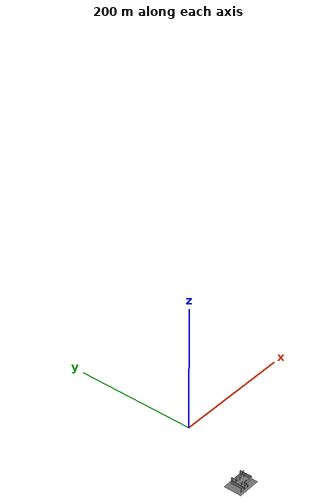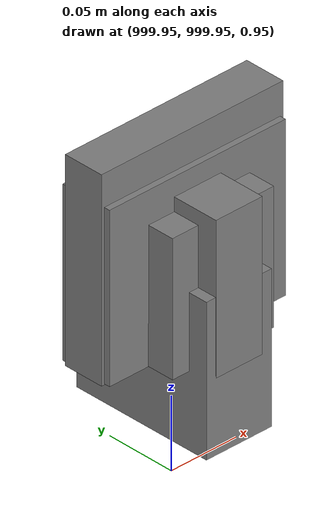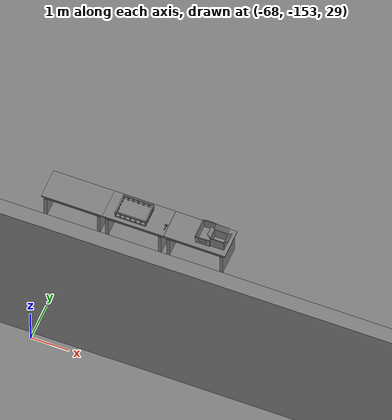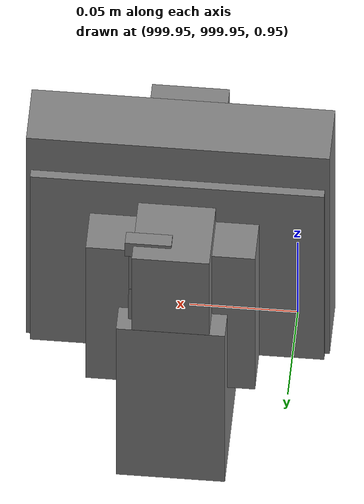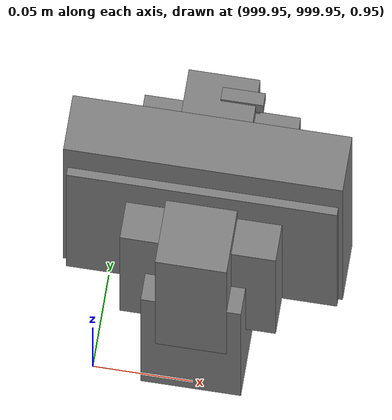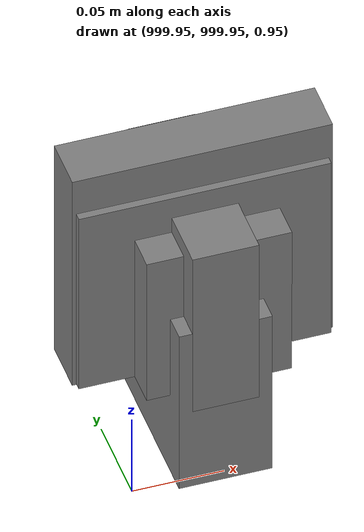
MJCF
<mujoco>
    <option gravity="0.000000000 0.000000000 -9.810000420" timestep="0.0049999999" integrator="implicitfast" density="1.225" viscosity="1.8000001e-05" noslip_iterations="10" iterations="100" sdf_iterations="50">
        <flag multiccd="disable"/>
    </option>
    <size memory="1000M"/>
    <compiler coordinate="local"/>
    <worldbody>
        <light cutoff="30" pos="0 1 1" dir="0 -1 -2"/>
        <light cutoff="30" pos="0 -1 1" dir="0 1 -2"/>
        <body pos="1000.000000000 1000.000000000 1.000000000" euler="0.000000000 0.000000000 180.000000000" name="openloong_gripper_2f85_fix_base_usda_battery_01">
            <geom contype="1" conaffinity="1" density="1000" type="box" material="" rgba="0.500000000 0.500000000 0.500000000 1.000000000" solimp="0.899999976 0.949999988 0.001000000" friction="1.000000000 0.005000000 0.000100000" solref="0.020000000 1.000000000" margin="0" condim="3" group="0" pos="-0.011123657 -0.041940309 0.101691343" quat="1.000000000 0.000000000 0.000000000 0.000000000" size="0.010800000 0.003375000 0.004725000" name="openloong_gripper_2f85_fix_base_usda_geom_1C741F43_7FB2_4C0E_B58D_BE8DAE66A5BD"/>
            <geom contype="1" conaffinity="1" density="1000" type="box" material="" rgba="0.500000000 0.500000000 0.500000000 1.000000000" solimp="0.899999976 0.949999988 0.001000000" friction="1.000000000 0.005000000 0.000100000" solref="0.020000000 1.000000000" margin="0" condim="3" group="0" pos="-0.010876465 -0.044247437 0.047066893" quat="0.998702705 -0.050920475 0.000000000 0.000000000" size="0.009450001 0.002700000 0.024975000" name="openloong_gripper_2f85_fix_base_usda_geom_0A806B25_3087_4A71_B558_4AC9E4C5B480"/>
            <geom contype="1" conaffinity="1" density="1000" type="box" material="" rgba="0.500000000 0.500000000 0.500000000 1.000000000" solimp="0.899999976 0.949999988 0.001000000" friction="1.000000000 0.005000000 0.000100000" solref="0.020000000 1.000000000" margin="0" condim="3" group="0" pos="-0.001235962 -0.000659180 0.047381196" quat="1.000000000 0.000000000 0.000000000 0.000000000" size="0.039420001 0.039150000 0.047250003" name="openloong_gripper_2f85_fix_base_usda_geom_751C94AE_42AE_4B10_A0BC_EC1190E28969"/>
            <geom contype="1" conaffinity="1" density="1000" type="box" material="" rgba="0.500000000 0.500000000 0.500000000 1.000000000" solimp="0.899999976 0.949999988 0.001000000" friction="1.000000000 0.005000000 0.000100000" solref="0.020000000 1.000000000" margin="0" condim="3" group="0" pos="-0.010876465 -0.039138794 0.009851727" quat="1.000000000 0.000000000 0.000000000 0.000000000" size="0.009450001 0.010800000 0.013500000" name="openloong_gripper_2f85_fix_base_usda_geom_C729E833_C81F_4A04_B7AC_E4407DAEBD9F"/>
            <geom contype="1" conaffinity="1" density="1000" type="box" material="" rgba="0.500000000 0.500000000 0.500000000 1.000000000" solimp="0.899999976 0.949999988 0.001000000" friction="1.000000000 0.005000000 0.000100000" solref="0.020000000 1.000000000" margin="0" condim="3" group="0" pos="-0.010876465 -0.041528322 0.071508206" quat="1.000000000 0.000000000 0.000000000 0.000000000" size="0.009450001 0.002700000 0.027000001" name="openloong_gripper_2f85_fix_base_usda_geom_7F0927EC_0412_467A_AEA0_3C4F7DE66B58"/>
            <freejoint name="openloong_gripper_2f85_fix_base_usda_battery_01_joint"/>
            <site size="0.005000000 0.005000000 0.005000000" rgba="0.500000000 0.500000000 0.500000000 1.000000000" pos="0.000000000 0.000000000 0.000000000" quat="0.999961913 0.008726500 0.000000000 0.000000000" group="0" type="sphere" name="openloong_gripper_2f85_fix_base_usda_battery_01site"/>
        </body>
        <body pos="1000.000000000 1000.000000000 1.000000000" euler="0.000000000 0.000000000 180.000000000" name="openloong_gripper_2f85_fix_base_usda_cpu_fan">
            <geom contype="1" conaffinity="1" density="1000" type="box" material="" rgba="0.500000000 0.500000000 0.500000000 1.000000000" solimp="0.899999976 0.949999988 0.001000000" friction="1.000000000 0.005000000 0.000100000" solref="0.020000000 1.000000000" margin="0" condim="3" group="0" pos="0.000000000 0.000000000 0.070034981" quat="0.000000000 0.000000000 0.000000000 1.000000000" size="0.070700005 0.014699999 0.070700005" name="openloong_gripper_2f85_fix_base_usda_geom_79461D12_628F_4E94_BD35_35B7AC32762E"/>
            <freejoint name="openloong_gripper_2f85_fix_base_usda_cpu_fan_joint"/>
            <site size="0.005000000 0.005000000 0.005000000" rgba="0.500000000 0.500000000 0.500000000 1.000000000" pos="0.000000000 0.000000000 0.000000000" quat="0.999961913 0.008726535 0.000000000 0.000000000" group="0" type="sphere" name="openloong_gripper_2f85_fix_base_usda_cpu_fancsite"/>
        </body>
        <body pos="1000.000000000 1000.000000000 1.000000000" euler="0.000000000 0.000000000 180.000000000" name="openloong_gripper_2f85_fix_base_usda_wifi_box">
            <geom contype="1" conaffinity="1" density="1000" type="box" material="" rgba="0.500000000 0.500000000 0.500000000 1.000000000" solimp="0.899999976 0.949999988 0.001000000" friction="1.000000000 0.005000000 0.000100000" solref="0.020000000 1.000000000" margin="0" condim="3" group="0" pos="0.000000000 0.000000000 0.058978677" quat="0.000000000 0.000000047 0.000000000 1.000000000" size="0.068499997 0.018999999 0.059000000" name="openloong_gripper_2f85_fix_base_usda_geom_80BD6618_720A_4704_B95A_544124E8B810"/>
            <freejoint name="openloong_gripper_2f85_fix_base_usda_wifi_box_joint"/>
            <site size="0.005000000 0.005000000 0.005000000" rgba="0.500000000 0.500000000 0.500000000 1.000000000" pos="0.000000000 0.000000000 0.000000000" quat="0.999961913 0.008726500 0.000000000 0.000000000" group="0" type="sphere" name="openloong_gripper_2f85_fix_base_usda_wifi_boxsite"/>
        </body>
        <body pos="-66.090515137 -149.571960449 31.165094376" euler="62.247989655 -31.320240021 90.439476013" mocap="true" name="spotlight6_SpotLight"/>
        <body pos="1000.000000000 1000.000000000 1.000000000" euler="0.000011953 0.000005123 -179.999984741" name="openloong_gripper_2f85_fix_base_usda_intel_box">
            <geom contype="1" conaffinity="1" density="1000" type="box" material="" rgba="0.500000000 0.500000000 0.500000000 1.000000000" solimp="0.899999976 0.949999988 0.001000000" friction="1.000000000 0.005000000 0.000100000" solref="0.020000000 1.000000000" margin="0" condim="3" group="0" pos="0.000000000 -0.000067139 0.000082284" quat="0.707106709 0.000000225 0.000000253 0.707106650" size="0.052800003 0.025300000 0.052800003" name="openloong_gripper_2f85_fix_base_usda_geom_F1C56D80_AE4E_4DA1_BDE1_1B7CE86ADC01"/>
            <freejoint name="openloong_gripper_2f85_fix_base_usda_intel_box_joint"/>
            <site size="0.005000000 0.005000000 0.005000000" rgba="0.500000000 0.500000000 0.500000000 1.000000000" pos="0.000000000 0.000000000 0.000000000" quat="0.999961913 0.008726500 0.000000000 0.000000000" group="0" type="sphere" name="openloong_gripper_2f85_fix_base_usda_intel_boxsite"/>
        </body>
        <body pos="1000.000000000 999.999938965 1.000000000" euler="0.000000000 0.000000000 180.000000000" name="openloong_gripper_2f85_fix_base_usda_intelcore_i5">
            <geom contype="1" conaffinity="1" density="1000" type="box" material="" rgba="0.500000000 0.500000000 0.500000000 1.000000000" solimp="0.899999976 0.949999988 0.001000000" friction="1.000000000 0.005000000 0.000100000" solref="0.020000000 1.000000000" margin="0" condim="3" group="0" pos="0.000000000 0.000000000 0.051722717" quat="0.707106709 0.000000000 0.000000000 -0.707106769" size="0.052800000 0.018080002 0.052800000" name="openloong_gripper_2f85_fix_base_usda_geom_645CF533_7788_48EB_9CA7_9C114D439015"/>
            <freejoint name="openloong_gripper_2f85_fix_base_usda_intelcore_i5_joint"/>
            <site size="0.005000000 0.005000000 0.005000000" rgba="0.500000000 0.500000000 0.500000000 1.000000000" pos="0.000000000 0.000000000 0.000000000" quat="0.999961913 0.008726534 0.000000000 0.000000000" group="0" type="sphere" name="openloong_gripper_2f85_fix_base_usda_intelcore_i5site"/>
        </body>
        <body pos="-66.174263000 -149.509643555 31.171018600" euler="-90.584854126 70.545822144 -37.211559296" mocap="true" name="spotlight2_SpotLight"/>
        <body pos="-66.371902466 -148.829513550 31.162563324" euler="-103.696693420 -43.481529236 31.244432449" mocap="true" name="spotlight4_SpotLight"/>
        <body pos="-64.866622925 -149.383972168 30.183746338" euler="89.999984741 89.999946594 0.000000000" name="openloong_gripper_2f85_fix_base_usda_bluebox_01">
            <geom contype="1" conaffinity="1" density="1000" type="box" material="" rgba="0.500000000 0.500000000 0.500000000 1.000000000" solimp="0.899999976 0.949999988 0.001000000" friction="1.000000000 0.005000000 0.000100000" solref="0.020000000 1.000000000" margin="0" condim="3" group="0" pos="0.276580811 0.187225342 0.000068665" quat="0.707106948 0.000077471 0.707106352 0.000077486" size="0.100000001 0.057999998 0.010000000" name="openloong_gripper_2f85_fix_base_usda_geom_696A9F14_A5D0_4B78_B19F_16C8DE6841E7"/>
            <geom contype="1" conaffinity="1" density="1000" type="box" material="" rgba="0.500000000 0.500000000 0.500000000 1.000000000" solimp="0.899999976 0.949999988 0.001000000" friction="1.000000000 0.005000000 0.000100000" solref="0.020000000 1.000000000" margin="0" condim="3" group="0" pos="0.000000000 0.002883911 0.000000000" quat="0.999999881 0.000000000 0.000000000 0.000000000" size="0.254000008 0.003000000 0.172000006" name="openloong_gripper_2f85_fix_base_usda_geom_D65CE33F_D365_4F09_A2F5_AE03A830CC23"/>
            <geom contype="1" conaffinity="1" density="1000" type="box" material="" rgba="0.500000000 0.500000000 0.500000000 1.000000000" solimp="0.899999976 0.949999988 0.001000000" friction="1.000000000 0.005000000 0.000100000" solref="0.020000000 1.000000000" margin="0" condim="3" group="0" pos="0.000000000 0.124874115 0.173484802" quat="0.999796331 0.020176515 -0.000000015 0.000000030" size="0.259999990 0.119999997 0.007000000" name="openloong_gripper_2f85_fix_base_usda_geom_A2F50289_9987_4301_B233_F19262048E74"/>
            <geom contype="1" conaffinity="1" density="1000" type="box" material="" rgba="0.500000000 0.500000000 0.500000000 1.000000000" solimp="0.899999976 0.949999988 0.001000000" friction="1.000000000 0.005000000 0.000100000" solref="0.020000000 1.000000000" margin="0" condim="3" group="0" pos="0.000000000 0.124874115 -0.173469543" quat="0.999796331 -0.020176545 -0.000000015 0.000000000" size="0.259999990 0.119999997 0.007000000" name="openloong_gripper_2f85_fix_base_usda_geom_A6755270_EFCC_47CD_B1EB_E744F575A9E9"/>
            <geom contype="1" conaffinity="1" density="1000" type="box" material="" rgba="0.500000000 0.500000000 0.500000000 1.000000000" solimp="0.899999976 0.949999988 0.001000000" friction="1.000000000 0.005000000 0.000100000" solref="0.020000000 1.000000000" margin="0" condim="3" group="0" pos="0.000000000 0.214008331 0.188980103" quat="0.999912977 0.013176724 0.000000015 0.000000000" size="0.259999990 0.029999999 0.012500000" name="openloong_gripper_2f85_fix_base_usda_geom_91AFF517_EB88_4366_990B_C16C203B7D2E"/>
            <geom contype="1" conaffinity="1" density="1000" type="box" material="" rgba="0.500000000 0.500000000 0.500000000 1.000000000" solimp="0.899999976 0.949999988 0.001000000" friction="1.000000000 0.005000000 0.000100000" solref="0.020000000 1.000000000" margin="0" condim="3" group="0" pos="-0.258361816 0.125289917 0.001876831" quat="0.702796936 -0.020792112 0.710783124 0.020769298" size="0.189999998 0.119999997 0.009000000" name="openloong_gripper_2f85_fix_base_usda_geom_45FB450F_654D_4991_ACD8_7B19AE6892B4"/>
            <geom contype="1" conaffinity="1" density="1000" type="box" material="" rgba="0.500000000 0.500000000 0.500000000 1.000000000" solimp="0.899999976 0.949999988 0.001000000" friction="1.000000000 0.005000000 0.000100000" solref="0.020000000 1.000000000" margin="0" condim="3" group="0" pos="0.000000000 0.214008331 -0.188980103" quat="0.999912977 -0.013176769 0.000000030 0.000000015" size="0.259999990 0.029999999 0.012500000" name="openloong_gripper_2f85_fix_base_usda_geom_34EA485D_A06F_4DE4_ACB9_1E1456C61209"/>
            <geom contype="1" conaffinity="1" density="1000" type="box" material="" rgba="0.500000000 0.500000000 0.500000000 1.000000000" solimp="0.899999976 0.949999988 0.001000000" friction="1.000000000 0.005000000 0.000100000" solref="0.020000000 1.000000000" margin="0" condim="3" group="0" pos="-0.276611328 0.187225342 0.000068665" quat="0.707106650 0.000077441 0.707106709 0.000077456" size="0.100000001 0.057999998 0.010000000" name="openloong_gripper_2f85_fix_base_usda_geom_F5F6F761_088D_43C7_A68A_F4FE147D6BFF"/>
            <geom contype="1" conaffinity="1" density="1000" type="box" material="" rgba="0.500000000 0.500000000 0.500000000 1.000000000" solimp="0.899999976 0.949999988 0.001000000" friction="1.000000000 0.005000000 0.000100000" solref="0.020000000 1.000000000" margin="0" condim="3" group="0" pos="0.258331299 0.125289917 0.001876831" quat="0.702851415 0.018856421 0.710823774 -0.019329369" size="0.189999998 0.119999997 0.009000000" name="openloong_gripper_2f85_fix_base_usda_geom_19ECC273_ECBD_4A1E_B8A1_802423E8F0B2"/>
            <freejoint name="openloong_gripper_2f85_fix_base_usda_bluebox_01_joint"/>
            <site size="0.005000000 0.005000000 0.005000000" rgba="0.500000000 0.500000000 0.500000000 1.000000000" pos="0.000000000 0.000000000 0.000000000" quat="0.999961913 0.008726534 0.000000000 0.000000000" group="0" type="sphere" name="openloong_gripper_2f85_fix_base_usda_bluebox_01site"/>
        </body>
        <body pos="-64.496299744 -149.491867065 30.235729218" euler="0.000000000 0.000000000 89.999946594" name="openloong_gripper_2f85_fix_base_usda_cardboardbox_01">
            <geom contype="1" conaffinity="1" density="1000" type="box" material="" rgba="0.500000000 0.500000000 0.500000000 1.000000000" solimp="0.899999976 0.949999988 0.001000000" friction="1.000000000 0.005000000 0.000100000" solref="0.020000000 1.000000000" margin="0" condim="3" group="0" pos="-0.003166199 -0.004086494 0.005052090" quat="1.000000000 0.000000000 0.000000000 0.000000000" size="0.142499998 0.177500010 0.005000000" name="openloong_gripper_2f85_fix_base_usda_geom_AB6A5F80_D4E1_4425_83DF_1A612A0E286C"/>
            <geom contype="1" conaffinity="1" density="1000" type="box" material="" rgba="0.500000000 0.500000000 0.500000000 1.000000000" solimp="0.899999976 0.949999988 0.001000000" friction="1.000000000 0.005000000 0.000100000" solref="0.020000000 1.000000000" margin="0" condim="3" group="0" pos="-0.003166199 0.170316696 0.150570869" quat="1.000000000 0.000000000 0.000000000 0.000000000" size="0.142499998 0.005000000 0.149999991" name="openloong_gripper_2f85_fix_base_usda_geom_13C54B5D_C0DF_4CBD_A0C4_E130613633AF"/>
            <geom contype="1" conaffinity="1" density="1000" type="box" material="" rgba="0.500000000 0.500000000 0.500000000 1.000000000" solimp="0.899999976 0.949999988 0.001000000" friction="1.000000000 0.005000000 0.000100000" solref="0.020000000 1.000000000" margin="0" condim="3" group="0" pos="-0.147399902 -0.005307198 0.150570869" quat="1.000000000 0.000000000 0.000000000 0.000000000" size="0.005000000 0.177500010 0.149999991" name="openloong_gripper_2f85_fix_base_usda_geom_4FCF9146_1991_4858_9A00_8E4F7C020D58"/>
            <geom contype="1" conaffinity="1" density="1000" type="box" material="" rgba="0.500000000 0.500000000 0.500000000 1.000000000" solimp="0.899999976 0.949999988 0.001000000" friction="1.000000000 0.005000000 0.000100000" solref="0.020000000 1.000000000" margin="0" condim="3" group="0" pos="0.140275955 -0.005307198 0.150570869" quat="1.000000000 0.000000000 0.000000000 0.000000000" size="0.005000000 0.177500010 0.149999991" name="openloong_gripper_2f85_fix_base_usda_geom_7E820757_ABE3_45D3_8657_DE50EDBDB9A8"/>
            <geom contype="1" conaffinity="1" density="1000" type="box" material="" rgba="0.500000000 0.500000000 0.500000000 1.000000000" solimp="0.899999976 0.949999988 0.001000000" friction="1.000000000 0.005000000 0.000100000" solref="0.020000000 1.000000000" margin="0" condim="3" group="0" pos="-0.003166199 -0.181550980 0.150570869" quat="1.000000000 0.000000000 0.000000000 0.000000000" size="0.142499998 0.005000000 0.149999991" name="openloong_gripper_2f85_fix_base_usda_geom_04071B0D_D2EB_4BA6_A782_165F90066BC4"/>
            <freejoint name="openloong_gripper_2f85_fix_base_usda_cardboardbox_01_joint"/>
            <site size="0.005000000 0.005000000 0.005000000" rgba="0.500000000 0.500000000 0.500000000 1.000000000" pos="0.000000000 0.000000000 0.000000000" quat="0.999961913 0.008726535 0.000000000 0.000000000" group="0" type="sphere" name="openloong_gripper_2f85_fix_base_usda_site_2336A46B_7C8A_4364_8A69_A056FC806BC4"/>
            <body pos="0.139160156 -0.004048347 0.301930904" euler="-179.999954224 49.383502960 179.999954224" name="openloong_gripper_2f85_fix_base_usda_A1_006">
                <geom contype="1" conaffinity="1" density="1000" type="box" material="" rgba="0.500000000 0.500000000 0.500000000 1.000000000" solimp="0.899999976 0.949999988 0.001000000" friction="1.000000000 0.005000000 0.000100000" solref="0.020000000 1.000000000" margin="0" condim="3" group="0" pos="-0.071587563 0.000009537 0.001745224" quat="0.999999881 0.000000000 0.000000000 0.000000000" size="0.071249999 0.179999992 0.002500000" name="openloong_gripper_2f85_fix_base_usda_geom_6A097454_B813_4032_9FD8_858729C409A4"/>
                <joint armature="0" stiffness="0.07" damping="0.0099999998" axis="0.000000 1.000000 0.000000" type="hinge" name="openloong_gripper_2f85_fix_base_usda_A1_006"/>
            </body>
            <body pos="-0.145902634 -0.004086494 0.301938057" euler="-180.000000000 -60.000011444 -180.000000000" name="openloong_gripper_2f85_fix_base_usda_A2_006">
                <geom contype="1" conaffinity="1" density="1000" type="box" material="" rgba="0.500000000 0.500000000 0.500000000 1.000000000" solimp="0.899999976 0.949999988 0.001000000" friction="1.000000000 0.005000000 0.000100000" solref="0.020000000 1.000000000" margin="0" condim="3" group="0" pos="0.071268082 0.000009537 0.002717972" quat="0.000002921 0.000000000 -0.000000030 0.999999881" size="0.071249999 0.179999992 0.002500000" name="openloong_gripper_2f85_fix_base_usda_geom_B079FE1B_973C_4C17_8A07_CC2FE3EA1671"/>
                <joint armature="0" stiffness="0.07" damping="0.0099999998" axis="0.000000 1.000000 0.000000" type="hinge" name="openloong_gripper_2f85_fix_base_usda_A2_006"/>
            </body>
            <body pos="-0.003385544 0.175991058 0.301930904" euler="-125.858116150 -0.000004561 0.000002331" name="openloong_gripper_2f85_fix_base_usda_B2_006">
                <geom contype="1" conaffinity="1" density="1000" type="box" material="" rgba="0.500000000 0.500000000 0.500000000 1.000000000" solimp="0.899999976 0.949999988 0.001000000" friction="1.000000000 0.005000000 0.000100000" solref="0.020000000 1.000000000" margin="0" condim="3" group="0" pos="0.000009537 -0.070939064 -0.002470016" quat="0.999614120 0.027776197 -0.000000015 0.000000030" size="0.137500003 0.064999998 0.005000000" name="openloong_gripper_2f85_fix_base_usda_geom_BE89F31B_3915_41FA_B220_3B85F1519456"/>
                <joint armature="0" stiffness="0.07" damping="0.0099999998" axis="1.000000 0.000000 0.000000" type="hinge" name="openloong_gripper_2f85_fix_base_usda_B2_006"/>
            </body>
            <body pos="-0.003385544 -0.184140205 0.301938057" euler="147.805557251 0.000000000 0.000000000" name="openloong_gripper_2f85_fix_base_usda_B1_006">
                <geom contype="1" conaffinity="1" density="1000" type="box" material="" rgba="0.500000000 0.500000000 0.500000000 1.000000000" solimp="0.899999976 0.949999988 0.001000000" friction="1.000000000 0.005000000 0.000100000" solref="0.020000000 1.000000000" margin="0" condim="3" group="0" pos="-0.000028610 0.070202351 -0.002703667" quat="0.999614179 -0.027776167 0.000000000 0.000000000" size="0.137500003 0.064999998 0.005000000" name="openloong_gripper_2f85_fix_base_usda_geom_427DA5B8_10E9_4526_8310_7162D066AAC1"/>
                <joint armature="0" stiffness="0.07" damping="0.0099999998" axis="1.000000 0.000000 0.000000" type="hinge" name="openloong_gripper_2f85_fix_base_usda_B1_006"/>
            </body>
        </body>
        <body pos="-65.882858276 -149.481979370 30.229999542" euler="-64.487716675 0.000000000 0.000000000" name="openloong_gripper_2f85_fix_base_usda_Barcode">
            <geom contype="1" conaffinity="1" density="1000" type="box" material="" rgba="0.500000000 0.500000000 0.500000000 1.000000000" solimp="0.899999976 0.949999988 0.001000000" friction="1.000000000 0.005000000 0.000100000" solref="0.020000000 1.000000000" margin="0" condim="3" group="0" pos="0.000000000 0.013038635 0.001419067" quat="0.000000000 0.000000000 0.000000000 1.000000119" size="0.034000002 0.010000000 0.017999999" name="openloong_gripper_2f85_fix_base_usda_geom_78D7652A_3AFF_4220_A386_AF26A8011B7C"/>
            <geom contype="1" conaffinity="1" density="1000" type="box" material="" rgba="0.500000000 0.500000000 0.500000000 1.000000000" solimp="0.899999976 0.949999988 0.001000000" friction="1.000000000 0.005000000 0.000100000" solref="0.020000000 1.000000000" margin="0" condim="3" group="0" pos="0.000000000 -0.035301208 -0.007095337" quat="0.000000000 0.000000000 -0.043619365 0.999048233" size="0.028999999 0.010000000 0.020000000" name="openloong_gripper_2f85_fix_base_usda_geom_3E6F7A08_773F_4F7C_82CC_ABCF79BDE05D"/>
            <geom contype="1" conaffinity="1" density="1000" type="box" material="" rgba="0.500000000 0.500000000 0.500000000 1.000000000" solimp="0.899999976 0.949999988 0.001000000" friction="1.000000000 0.005000000 0.000100000" solref="0.020000000 1.000000000" margin="0" condim="3" group="0" pos="0.000000000 -0.043411255 -0.011749268" quat="0.922262907 0.386563420 0.000000000 0.000000000" size="0.026000001 0.010000000 0.020000000" name="openloong_gripper_2f85_fix_base_usda_geom_DBB8C1D1_EB2E_4E6E_949E_8A7733D90E4D"/>
            <geom contype="1" conaffinity="1" density="1000" type="box" material="" rgba="0.500000000 0.500000000 0.500000000 1.000000000" solimp="0.899999976 0.949999988 0.001000000" friction="1.000000000 0.005000000 0.000100000" solref="0.020000000 1.000000000" margin="0" condim="3" group="0" pos="0.000000000 -0.016967773 -0.031860352" quat="0.000000000 0.000000000 0.000000000 1.000000119" size="0.008000000 0.010000000 0.013000000" name="openloong_gripper_2f85_fix_base_usda_geom_4D308D1C_3026_4D69_9BB8_F11FCDA2345C"/>
            <geom contype="1" conaffinity="1" density="1000" type="box" material="" rgba="0.500000000 0.500000000 0.500000000 1.000000000" solimp="0.899999976 0.949999988 0.001000000" friction="1.000000000 0.005000000 0.000100000" solref="0.020000000 1.000000000" margin="0" condim="3" group="0" pos="0.000000000 -0.001869202 0.000312805" quat="0.953716993 0.300705761 0.000000000 0.000000000" size="0.032000002 0.010000000 0.018999999" name="openloong_gripper_2f85_fix_base_usda_geom_56DF8576_64E6_4700_A575_1E32A5AEC218"/>
            <geom contype="1" conaffinity="1" density="1000" type="box" material="" rgba="0.500000000 0.500000000 0.500000000 1.000000000" solimp="0.899999976 0.949999988 0.001000000" friction="1.000000000 0.005000000 0.000100000" solref="0.020000000 1.000000000" margin="0" condim="3" group="0" pos="0.000000000 -0.019531250 -0.003173828" quat="0.953716993 0.300705761 0.000000000 0.000000000" size="0.030999999 0.010000000 0.020000000" name="openloong_gripper_2f85_fix_base_usda_geom_EC328B7C_2D58_4E80_8D81_2FE152FD1FCF"/>
            <geom contype="1" conaffinity="1" density="1000" type="box" material="" rgba="0.500000000 0.500000000 0.500000000 1.000000000" solimp="0.899999976 0.949999988 0.001000000" friction="1.000000000 0.005000000 0.000100000" solref="0.020000000 1.000000000" margin="0" condim="3" group="0" pos="0.000000000 -0.035301208 -0.007095337" quat="0.953716993 0.300705761 0.000000000 0.000000000" size="0.028999999 0.010000000 0.020000000" name="openloong_gripper_2f85_fix_base_usda_geom_0106BE9D_788C_474C_BF12_3E56954C7ABC"/>
            <geom contype="1" conaffinity="1" density="1000" type="box" material="" rgba="0.500000000 0.500000000 0.500000000 1.000000000" solimp="0.899999976 0.949999988 0.001000000" friction="1.000000000 0.005000000 0.000100000" solref="0.020000000 1.000000000" margin="0" condim="3" group="0" pos="0.000000000 -0.042617798 -0.071121216" quat="0.000000000 0.000000000 0.000000000 1.000000119" size="0.013000000 0.021000000 0.059999999" name="openloong_gripper_2f85_fix_base_usda_geom_AD0A4894_B87F_4128_987F_EE4D27E6E792"/>
            <freejoint name="openloong_gripper_2f85_fix_base_usda_Barcode_joint"/>
            <site size="0.005000000 0.005000000 0.005000000" rgba="0.500000000 0.500000000 0.500000000 1.000000000" pos="0.000000000 0.000000000 0.000000000" quat="1.000000000 0.000000000 0.000000000 0.000000000" group="0" type="sphere" name="openloong_gripper_2f85_fix_base_usda_Barcode_site"/>
        </body>
        <body pos="-66.745018005 -149.392349243 30.184000015" euler="0.000000000 0.000000000 89.999946594" name="[22331115874250]_Basket_01">
            <geom contype="1" conaffinity="1" density="1000" type="box" material="" rgba="0.500000000 0.500000000 0.500000000 1.000000000" solimp="0.899999976 0.949999988 0.001000000" friction="1.000000000 0.005000000 0.000100000" solref="0.020000000 1.000000000" margin="0" condim="3" group="0" pos="-0.052425385 0.389207840 0.089787483" quat="0.707107008 0.000000000 0.000000000 0.707106411" size="0.014249999 0.014249999 0.059999999" name="[22331115874250]_geom_4D3C2FBE_27D8_4972_A6CA_F03A10833BF4"/>
            <geom contype="1" conaffinity="1" density="1000" type="box" material="" rgba="0.500000000 0.500000000 0.500000000 1.000000000" solimp="0.899999976 0.949999988 0.001000000" friction="1.000000000 0.005000000 0.000100000" solref="0.020000000 1.000000000" margin="0" condim="3" group="0" pos="0.264015198 -0.133043289 0.089787483" quat="0.707107008 0.000000000 0.000000000 0.707106411" size="0.014249999 0.014249999 0.059999999" name="[22331115874250]_geom_B5C60218_7F07_4DF8_83BC_A9DEB67B5BE2"/>
            <geom contype="1" conaffinity="1" density="1000" type="box" material="" rgba="0.500000000 0.500000000 0.500000000 1.000000000" solimp="0.899999976 0.949999988 0.001000000" friction="1.000000000 0.005000000 0.000100000" solref="0.020000000 1.000000000" margin="0" condim="3" group="0" pos="-0.264015198 -0.265548706 0.089793205" quat="0.707107008 0.000000000 0.000000000 0.707106411" size="0.014249999 0.014249999 0.059999999" name="[22331115874250]_geom_B8F6EF58_2C46_4DA1_BD77_4B49F7B70AE3"/>
            <geom contype="1" conaffinity="1" density="1000" type="box" material="" rgba="0.500000000 0.500000000 0.500000000 1.000000000" solimp="0.899999976 0.949999988 0.001000000" friction="1.000000000 0.005000000 0.000100000" solref="0.020000000 1.000000000" margin="0" condim="3" group="0" pos="-0.160263062 -0.389322281 0.089793205" quat="0.707107008 0.000000000 0.000000000 0.707106411" size="0.014249999 0.014249999 0.059999999" name="[22331115874250]_geom_771D4CC6_BA00_4836_B49E_9C4A1E29976C"/>
            <geom contype="1" conaffinity="1" density="1000" type="box" material="" rgba="0.500000000 0.500000000 0.500000000 1.000000000" solimp="0.899999976 0.949999988 0.001000000" friction="1.000000000 0.005000000 0.000100000" solref="0.020000000 1.000000000" margin="0" condim="3" group="0" pos="0.162265778 -0.389322281 0.089787483" quat="0.707107008 0.000000000 0.000000000 0.707106411" size="0.014249999 0.014249999 0.059999999" name="[22331115874250]_geom_72258B40_B267_4A6A_A696_9689204A4D5C"/>
            <geom contype="1" conaffinity="1" density="1000" type="box" material="" rgba="0.500000000 0.500000000 0.500000000 1.000000000" solimp="0.899999976 0.949999988 0.001000000" friction="1.000000000 0.005000000 0.000100000" solref="0.020000000 1.000000000" margin="0" condim="3" group="0" pos="0.264015198 0.389207840 0.089787483" quat="0.707107008 0.000000000 0.000000000 0.707106411" size="0.014249999 0.014249999 0.059999999" name="[22331115874250]_geom_14E399A6_4A33_43C1_B6A0_2550F5ABBED1"/>
            <geom contype="1" conaffinity="1" density="1000" type="box" material="" rgba="0.500000000 0.500000000 0.500000000 1.000000000" solimp="0.899999976 0.949999988 0.001000000" friction="1.000000000 0.005000000 0.000100000" solref="0.020000000 1.000000000" margin="0" condim="3" group="0" pos="-0.264015198 -0.133043289 0.089793205" quat="0.707107008 0.000000000 0.000000000 0.707106411" size="0.014249999 0.014249999 0.059999999" name="[22331115874250]_geom_6A228FB4_2981_46C0_A3FD_96507852957E"/>
            <geom contype="1" conaffinity="1" density="1000" type="box" material="" rgba="0.500000000 0.500000000 0.500000000 1.000000000" solimp="0.899999976 0.949999988 0.001000000" friction="1.000000000 0.005000000 0.000100000" solref="0.020000000 1.000000000" margin="0" condim="3" group="0" pos="-0.264026642 0.269256592 0.089793205" quat="0.707107008 0.000000000 0.000000000 0.707106411" size="0.014249999 0.014249999 0.059999999" name="[22331115874250]_geom_AEA6C224_9133_4B78_975D_973078846B4D"/>
            <geom contype="1" conaffinity="1" density="1000" type="box" material="" rgba="0.500000000 0.500000000 0.500000000 1.000000000" solimp="0.899999976 0.949999988 0.001000000" friction="1.000000000 0.005000000 0.000100000" solref="0.020000000 1.000000000" margin="0" condim="3" group="0" pos="0.054462433 0.389207840 0.089787483" quat="0.707107008 0.000000000 0.000000000 0.707106411" size="0.014249999 0.014249999 0.059999999" name="[22331115874250]_geom_33B7CCD5_0BDF_487C_8AC3_F961AACAEB2F"/>
            <geom contype="1" conaffinity="1" density="1000" type="box" material="" rgba="0.500000000 0.500000000 0.500000000 1.000000000" solimp="0.899999976 0.949999988 0.001000000" friction="1.000000000 0.005000000 0.000100000" solref="0.020000000 1.000000000" margin="0" condim="3" group="0" pos="0.054462433 -0.389322281 0.089787483" quat="0.707107008 0.000000000 0.000000000 0.707106411" size="0.014249999 0.014249999 0.059999999" name="[22331115874250]_geom_85047646_29E3_4B5A_B656_69736CD95864"/>
            <geom contype="1" conaffinity="1" density="1000" type="box" material="" rgba="0.500000000 0.500000000 0.500000000 1.000000000" solimp="0.899999976 0.949999988 0.001000000" friction="1.000000000 0.005000000 0.000100000" solref="0.020000000 1.000000000" margin="0" condim="3" group="0" pos="0.264015198 0.269256592 0.089793205" quat="0.707107008 0.000000000 0.000000000 0.707106411" size="0.014249999 0.014249999 0.059999999" name="[22331115874250]_geom_53B0D6D5_4A98_44B7_A05F_AD4BE6A80372"/>
            <geom contype="1" conaffinity="1" density="1000" type="box" material="" rgba="0.500000000 0.500000000 0.500000000 1.000000000" solimp="0.899999976 0.949999988 0.001000000" friction="1.000000000 0.005000000 0.000100000" solref="0.020000000 1.000000000" margin="0" condim="3" group="0" pos="0.264015198 -0.389322281 0.089787483" quat="0.707107008 0.000000000 0.000000000 0.707106411" size="0.014249999 0.014249999 0.059999999" name="[22331115874250]_geom_9381CF01_C5B0_4D42_8EF5_A01DD2EDB04D"/>
            <geom contype="1" conaffinity="1" density="1000" type="box" material="" rgba="0.500000000 0.500000000 0.500000000 1.000000000" solimp="0.899999976 0.949999988 0.001000000" friction="1.000000000 0.005000000 0.000100000" solref="0.020000000 1.000000000" margin="0" condim="3" group="0" pos="0.000000000 0.000000000 0.015998840" quat="0.707107008 0.000000000 0.000000000 0.707106411" size="0.403499991 0.279000014 0.015750000" name="[22331115874250]_geom_296A33B8_6E0E_4C6E_83B7_9C37F3F2E074"/>
            <geom contype="1" conaffinity="1" density="1000" type="box" material="" rgba="0.500000000 0.500000000 0.500000000 1.000000000" solimp="0.899999976 0.949999988 0.001000000" friction="1.000000000 0.005000000 0.000100000" solref="0.020000000 1.000000000" margin="0" condim="3" group="0" pos="0.000000000 -0.389476776 0.163619041" quat="0.707107008 0.000000000 0.000000000 0.707106411" size="0.015000000 0.277500004 0.015750000" name="[22331115874250]_geom_B8B63522_23BF_4231_990B_6DAB5E0791A9"/>
            <geom contype="1" conaffinity="1" density="1000" type="box" material="" rgba="0.500000000 0.500000000 0.500000000 1.000000000" solimp="0.899999976 0.949999988 0.001000000" friction="1.000000000 0.005000000 0.000100000" solref="0.020000000 1.000000000" margin="0" condim="3" group="0" pos="0.162265778 0.389207840 0.089787483" quat="0.707107008 0.000000000 0.000000000 0.707106411" size="0.014249999 0.014249999 0.059999999" name="[22331115874250]_geom_CCC6A19D_30C7_4F1D_9636_7C451B69AE2E"/>
            <geom contype="1" conaffinity="1" density="1000" type="box" material="" rgba="0.500000000 0.500000000 0.500000000 1.000000000" solimp="0.899999976 0.949999988 0.001000000" friction="1.000000000 0.005000000 0.000100000" solref="0.020000000 1.000000000" margin="0" condim="3" group="0" pos="0.000000000 0.389471054 0.163619041" quat="0.707107008 0.000000000 0.000000000 0.707106411" size="0.015000000 0.277500004 0.015750000" name="[22331115874250]_geom_218D5B8D_4A1B_4120_B483_B43D71AC976B"/>
            <geom contype="1" conaffinity="1" density="1000" type="box" material="" rgba="0.500000000 0.500000000 0.500000000 1.000000000" solimp="0.899999976 0.949999988 0.001000000" friction="1.000000000 0.005000000 0.000100000" solref="0.020000000 1.000000000" margin="0" condim="3" group="0" pos="-0.263511658 0.000000000 0.163619041" quat="0.707107008 0.000000000 0.000000000 0.707106411" size="0.403499991 0.015000000 0.015750000" name="[22331115874250]_geom_C5EF019A_DA41_4785_80F5_3672195D8601"/>
            <geom contype="1" conaffinity="1" density="1000" type="box" material="" rgba="0.500000000 0.500000000 0.500000000 1.000000000" solimp="0.899999976 0.949999988 0.001000000" friction="1.000000000 0.005000000 0.000100000" solref="0.020000000 1.000000000" margin="0" condim="3" group="0" pos="-0.264015198 0.141334534 0.089793205" quat="0.707107008 0.000000000 0.000000000 0.707106411" size="0.014249999 0.014249999 0.059999999" name="[22331115874250]_geom_B02FE6C2_97BF_421E_ADF2_763703B38BDB"/>
            <geom contype="1" conaffinity="1" density="1000" type="box" material="" rgba="0.500000000 0.500000000 0.500000000 1.000000000" solimp="0.899999976 0.949999988 0.001000000" friction="1.000000000 0.005000000 0.000100000" solref="0.020000000 1.000000000" margin="0" condim="3" group="0" pos="0.264015198 -0.265548706 0.089787483" quat="0.707107008 0.000000000 0.000000000 0.707106411" size="0.014249999 0.014249999 0.059999999" name="[22331115874250]_geom_25A50860_3DAF_4048_B457_67F75A026F78"/>
            <geom contype="1" conaffinity="1" density="1000" type="box" material="" rgba="0.500000000 0.500000000 0.500000000 1.000000000" solimp="0.899999976 0.949999988 0.001000000" friction="1.000000000 0.005000000 0.000100000" solref="0.020000000 1.000000000" margin="0" condim="3" group="0" pos="-0.160263062 0.389207840 0.089787483" quat="0.707107008 0.000000000 0.000000000 0.707106411" size="0.014249999 0.014249999 0.059999999" name="[22331115874250]_geom_1F95B225_B37B_4479_A63B_2934F4E47636"/>
            <geom contype="1" conaffinity="1" density="1000" type="box" material="" rgba="0.500000000 0.500000000 0.500000000 1.000000000" solimp="0.899999976 0.949999988 0.001000000" friction="1.000000000 0.005000000 0.000100000" solref="0.020000000 1.000000000" margin="0" condim="3" group="0" pos="-0.052425385 -0.389322281 0.089787483" quat="0.707107008 0.000000000 0.000000000 0.707106411" size="0.014249999 0.014249999 0.059999999" name="[22331115874250]_geom_D2AE77CD_9E63_47B8_9E68_28267D249C28"/>
            <geom contype="1" conaffinity="1" density="1000" type="box" material="" rgba="0.500000000 0.500000000 0.500000000 1.000000000" solimp="0.899999976 0.949999988 0.001000000" friction="1.000000000 0.005000000 0.000100000" solref="0.020000000 1.000000000" margin="0" condim="3" group="0" pos="-0.264026642 -0.389322281 0.089793205" quat="0.707107008 0.000000000 0.000000000 0.707106411" size="0.014249999 0.014249999 0.059999999" name="[22331115874250]_geom_D4759D8B_7BE3_4554_8EBD_D0E1D76FC2A1"/>
            <geom contype="1" conaffinity="1" density="1000" type="box" material="" rgba="0.500000000 0.500000000 0.500000000 1.000000000" solimp="0.899999976 0.949999988 0.001000000" friction="1.000000000 0.005000000 0.000100000" solref="0.020000000 1.000000000" margin="0" condim="3" group="0" pos="0.264015198 0.141334534 0.089787483" quat="0.707107008 0.000000000 0.000000000 0.707106411" size="0.014249999 0.014249999 0.059999999" name="[22331115874250]_geom_89DE3ED1_D019_44BE_A8E5_EEBF89EAB551"/>
            <geom contype="1" conaffinity="1" density="1000" type="box" material="" rgba="0.500000000 0.500000000 0.500000000 1.000000000" solimp="0.899999976 0.949999988 0.001000000" friction="1.000000000 0.005000000 0.000100000" solref="0.020000000 1.000000000" margin="0" condim="3" group="0" pos="-0.264015198 0.389207840 0.089793205" quat="0.707107008 0.000000000 0.000000000 0.707106411" size="0.014249999 0.014249999 0.059999999" name="[22331115874250]_geom_5DC52A24_CB7B_4750_AFF0_38D60B6765A4"/>
            <geom contype="1" conaffinity="1" density="1000" type="box" material="" rgba="0.500000000 0.500000000 0.500000000 1.000000000" solimp="0.899999976 0.949999988 0.001000000" friction="1.000000000 0.005000000 0.000100000" solref="0.020000000 1.000000000" margin="0" condim="3" group="0" pos="0.264015198 0.004480362 0.089787483" quat="0.707107008 0.000000000 0.000000000 0.707106411" size="0.014249999 0.014249999 0.059999999" name="[22331115874250]_geom_D53A9C9D_D950_46E9_AECE_B763E4D9CE4C"/>
            <geom contype="1" conaffinity="1" density="1000" type="box" material="" rgba="0.500000000 0.500000000 0.500000000 1.000000000" solimp="0.899999976 0.949999988 0.001000000" friction="1.000000000 0.005000000 0.000100000" solref="0.020000000 1.000000000" margin="0" condim="3" group="0" pos="0.263694763 -0.000011444 0.163619041" quat="0.707107008 0.000000000 0.000000000 0.707106411" size="0.403499991 0.015000000 0.015750000" name="[22331115874250]_geom_D7E55E21_7C68_4096_992A_3AD7540673CD"/>
            <geom contype="1" conaffinity="1" density="1000" type="box" material="" rgba="0.500000000 0.500000000 0.500000000 1.000000000" solimp="0.899999976 0.949999988 0.001000000" friction="1.000000000 0.005000000 0.000100000" solref="0.020000000 1.000000000" margin="0" condim="3" group="0" pos="-0.264015198 0.004480362 0.089793205" quat="0.707107008 0.000000000 0.000000000 0.707106411" size="0.014249999 0.014249999 0.059999999" name="[22331115874250]_geom_FD6E7291_431A_42AD_BC1F_97B774404097"/>
            <freejoint name="[22331115874250]_joint_900ABEA9_7E9A_4218_A20B_D9191F725E49"/>
        </body>
        <body pos="0.000000000 0.000000000 0.000000000" euler="0.000000000 0.000000000 0.000000000" name="Static Objects_Static Objects">
            <geom contype="1" conaffinity="1" density="1000" type="box" material="" rgba="0.500000000 0.500000000 0.500000000 1.000000000" solimp="0.899999976 0.949999988 0.001000000" friction="1.000000000 0.005000000 0.000100000" solref="0.020000000 1.000000000" margin="0" condim="3" group="0" pos="-67.544113159 -149.365814209 29.727830887" quat="0.500000417 0.499999970 0.499999553 0.499999970" size="0.381000012 0.319999993 0.041000001" name="Static Objects_geom_EFC2A4CF_1BF1_48CC_8303_0AF3CFB44631"/>
            <geom contype="1" conaffinity="1" density="1000" type="box" material="" rgba="0.500000000 0.500000000 0.500000000 1.000000000" solimp="0.899999976 0.949999988 0.001000000" friction="1.000000000 0.005000000 0.000100000" solref="0.020000000 1.000000000" margin="0" condim="3" group="0" pos="-68.239501953 -149.365814209 30.086868286" quat="0.500000417 0.499999970 0.499999553 0.499999970" size="0.370999992 0.039500002 0.745000005" name="Static Objects_geom_539E6D5F_2D4D_40D4_99E4_F6D5CFE01EEB"/>
            <geom contype="1" conaffinity="1" density="1000" type="box" material="" rgba="0.500000000 0.500000000 0.500000000 1.000000000" solimp="0.899999976 0.949999988 0.001000000" friction="1.000000000 0.005000000 0.000100000" solref="0.020000000 1.000000000" margin="0" condim="3" group="0" pos="-68.239501953 -149.365814209 30.147235870" quat="0.500000417 0.499999970 0.499999553 0.499999970" size="0.400000006 0.022000000 0.800000012" name="Static Objects_geom_B669E5D3_70D3_43F9_A095_DAC3C1909120"/>
            <geom contype="1" conaffinity="1" density="1000" type="box" material="" rgba="0.500000000 0.500000000 0.500000000 1.000000000" solimp="0.899999976 0.949999988 0.001000000" friction="1.000000000 0.005000000 0.000100000" solref="0.020000000 1.000000000" margin="0" condim="3" group="0" pos="-68.934890747 -149.365814209 29.727830887" quat="0.500000417 0.499999970 0.499999553 0.499999970" size="0.381000012 0.319999993 0.041000001" name="Static Objects_geom_DF2FA4CC_C463_4FE8_9592_5988D426FF23"/>
            <geom contype="1" conaffinity="1" density="1000" type="box" material="" rgba="0.500000000 0.500000000 0.500000000 1.000000000" solimp="0.899999976 0.949999988 0.001000000" friction="1.000000000 0.005000000 0.000100000" solref="0.020000000 1.000000000" margin="0" condim="3" group="0" pos="-68.239501953 -149.365814209 29.561563492" quat="0.500000417 0.499999970 0.499999553 0.499999970" size="0.020000000 0.022000000 0.660000026" name="Static Objects_geom_F5B86019_9898_498A_9D34_412D149B9844"/>
            <geom contype="1" conaffinity="1" density="1000" type="box" material="" rgba="0.500000000 0.500000000 0.500000000 1.000000000" solimp="0.899999976 0.949999988 0.001000000" friction="1.000000000 0.005000000 0.000100000" solref="0.020000000 1.000000000" margin="0" condim="3" group="0" pos="-65.945671082 -149.365814209 29.727830887" quat="0.500000417 0.499999970 0.499999553 0.499999970" size="0.381000012 0.319999993 0.041000001" name="Static Objects_geom_7E846EC2_91AD_4E1F_9B49_2BAAB14A52D2"/>
            <geom contype="1" conaffinity="1" density="1000" type="box" material="" rgba="0.500000000 0.500000000 0.500000000 1.000000000" solimp="0.899999976 0.949999988 0.001000000" friction="1.000000000 0.005000000 0.000100000" solref="0.020000000 1.000000000" margin="0" condim="3" group="0" pos="-66.641059875 -149.365814209 30.086868286" quat="0.500000417 0.499999970 0.499999553 0.499999970" size="0.370999992 0.039500002 0.745000005" name="Static Objects_geom_DE34A99E_4DC0_4DE1_A715_DFA9F3751CEB"/>
            <geom contype="1" conaffinity="1" density="1000" type="box" material="" rgba="0.500000000 0.500000000 0.500000000 1.000000000" solimp="0.899999976 0.949999988 0.001000000" friction="1.000000000 0.005000000 0.000100000" solref="0.020000000 1.000000000" margin="0" condim="3" group="0" pos="-66.641059875 -149.365814209 30.147235870" quat="0.500000417 0.499999970 0.499999553 0.499999970" size="0.400000006 0.022000000 0.800000012" name="Static Objects_geom_12056B33_89F4_4733_B65A_78F59B61F606"/>
            <geom contype="1" conaffinity="1" density="1000" type="box" material="" rgba="0.500000000 0.500000000 0.500000000 1.000000000" solimp="0.899999976 0.949999988 0.001000000" friction="1.000000000 0.005000000 0.000100000" solref="0.020000000 1.000000000" margin="0" condim="3" group="0" pos="-67.336448669 -149.365814209 29.727830887" quat="0.500000417 0.499999970 0.499999553 0.499999970" size="0.381000012 0.319999993 0.041000001" name="Static Objects_geom_5DE6E887_3734_4768_B1A0_D5D97272EB02"/>
            <geom contype="1" conaffinity="1" density="1000" type="box" material="" rgba="0.500000000 0.500000000 0.500000000 1.000000000" solimp="0.899999976 0.949999988 0.001000000" friction="1.000000000 0.005000000 0.000100000" solref="0.020000000 1.000000000" margin="0" condim="3" group="0" pos="-66.641059875 -149.365814209 29.561563492" quat="0.500000417 0.499999970 0.499999553 0.499999970" size="0.020000000 0.022000000 0.660000026" name="Static Objects_geom_FC92EB04_39A5_45E9_8D18_3187D772AD0F"/>
            <geom contype="1" conaffinity="1" density="1000" type="box" material="" rgba="0.500000000 0.500000000 0.500000000 1.000000000" solimp="0.899999976 0.949999988 0.001000000" friction="1.000000000 0.005000000 0.000100000" solref="0.020000000 1.000000000" margin="0" condim="3" group="0" pos="-64.338577271 -149.365814209 29.727830887" quat="0.500000417 0.499999970 0.499999553 0.499999970" size="0.381000012 0.319999993 0.041000001" name="Static Objects_geom_899843FD_9E95_4C5F_ABFA_8F2F8CA2B921"/>
            <geom contype="1" conaffinity="1" density="1000" type="box" material="" rgba="0.500000000 0.500000000 0.500000000 1.000000000" solimp="0.899999976 0.949999988 0.001000000" friction="1.000000000 0.005000000 0.000100000" solref="0.020000000 1.000000000" margin="0" condim="3" group="0" pos="-65.033966064 -149.365814209 30.086868286" quat="0.500000417 0.499999970 0.499999553 0.499999970" size="0.370999992 0.039500002 0.745000005" name="Static Objects_geom_E1022745_6400_426C_AF71_2BF9B25AB00A"/>
            <geom contype="1" conaffinity="1" density="1000" type="box" material="" rgba="0.500000000 0.500000000 0.500000000 1.000000000" solimp="0.899999976 0.949999988 0.001000000" friction="1.000000000 0.005000000 0.000100000" solref="0.020000000 1.000000000" margin="0" condim="3" group="0" pos="-65.033966064 -149.365814209 30.147235870" quat="0.500000417 0.499999970 0.499999553 0.499999970" size="0.400000006 0.022000000 0.800000012" name="Static Objects_geom_F0F6C4DF_149F_4424_9005_752A8B99F131"/>
            <geom contype="1" conaffinity="1" density="1000" type="box" material="" rgba="0.500000000 0.500000000 0.500000000 1.000000000" solimp="0.899999976 0.949999988 0.001000000" friction="1.000000000 0.005000000 0.000100000" solref="0.020000000 1.000000000" margin="0" condim="3" group="0" pos="-65.729354858 -149.365814209 29.727830887" quat="0.500000417 0.499999970 0.499999553 0.499999970" size="0.381000012 0.319999993 0.041000001" name="Static Objects_geom_A7B2AB78_7F32_41AB_A238_08F1E9AB78EF"/>
            <geom contype="1" conaffinity="1" density="1000" type="box" material="" rgba="0.500000000 0.500000000 0.500000000 1.000000000" solimp="0.899999976 0.949999988 0.001000000" friction="1.000000000 0.005000000 0.000100000" solref="0.020000000 1.000000000" margin="0" condim="3" group="0" pos="-65.033966064 -149.365814209 29.561563492" quat="0.500000417 0.499999970 0.499999553 0.499999970" size="0.020000000 0.022000000 0.660000026" name="Static Objects_geom_FC120794_DAAC_4C15_8B04_8D22EF7E2E0D"/>
            <geom contype="1" conaffinity="1" density="1000" type="box" material="" rgba="0.500000000 0.500000000 0.500000000 1.000000000" solimp="0.899999976 0.949999988 0.001000000" friction="1.000000000 0.005000000 0.000100000" solref="0.020000000 1.000000000" margin="0" condim="3" group="0" pos="-61.754566193 -137.853729248 33.906845093" quat="0.707107067 0.000000000 0.000000000 0.707106471" size="0.759999990 0.759999990 4.500000000" name="Static Objects_geom_04936502_B4BD_49E2_9A35_DD5F7EFAC0B3"/>
            <geom contype="1" conaffinity="1" density="1000" type="box" material="" rgba="0.500000000 0.500000000 0.500000000 1.000000000" solimp="0.899999976 0.949999988 0.001000000" friction="1.000000000 0.005000000 0.000100000" solref="0.020000000 1.000000000" margin="0" condim="3" group="0" pos="-57.511135101 -144.927108765 31.707921982" quat="1.000000000 0.000000000 0.000000000 0.000000000" size="0.200000003 8.000000000 2.299999952" name="Static Objects_geom_CFE9E367_2056_454F_9898_E99E21C7B333"/>
            <geom contype="1" conaffinity="1" density="1000" type="box" material="" rgba="0.500000000 0.500000000 0.500000000 1.000000000" solimp="0.899999976 0.949999988 0.001000000" friction="1.000000000 0.005000000 0.000100000" solref="0.020000000 1.000000000" margin="0" condim="3" group="0" pos="-80.517646790 -157.574050903 31.688196182" quat="0.707107067 0.000000000 0.000000000 0.707106471" size="0.600000024 0.600000024 2.299999952" name="Static Objects_geom_36D761F4_38BF_4843_95CD_7C1567C3C2DC"/>
            <geom contype="1" conaffinity="1" density="1000" type="box" material="" rgba="0.500000000 0.500000000 0.500000000 1.000000000" solimp="0.899999976 0.949999988 0.001000000" friction="1.000000000 0.005000000 0.000100000" solref="0.020000000 1.000000000" margin="0" condim="3" group="0" pos="-80.711044312 -147.414932251 31.666158676" quat="1.000000000 0.000000000 0.000000000 0.000000000" size="0.200000003 10.000000000 2.299999952" name="Static Objects_geom_70B7FFF3_B67C_4647_88D1_A8853CD8A469"/>
            <geom contype="1" conaffinity="1" density="1000" type="box" material="" rgba="0.500000000 0.500000000 0.500000000 1.000000000" solimp="0.899999976 0.949999988 0.001000000" friction="1.000000000 0.005000000 0.000100000" solref="0.020000000 1.000000000" margin="0" condim="3" group="0" pos="-57.687217712 -137.434692383 31.688196182" quat="0.707107067 0.000000000 0.000000000 0.707106471" size="0.600000024 0.600000024 2.299999952" name="Static Objects_geom_CA3EB0E5_FDD6_44C6_93C1_086AF2CFD986"/>
            <geom contype="1" conaffinity="1" density="1000" type="box" material="" rgba="0.500000000 0.500000000 0.500000000 1.000000000" solimp="0.899999976 0.949999988 0.001000000" friction="1.000000000 0.005000000 0.000100000" solref="0.020000000 1.000000000" margin="0" condim="3" group="0" pos="-69.537033081 -140.263229370 31.714921951" quat="0.707107067 0.000000000 0.000000000 0.707106471" size="0.759999990 4.500000000 2.299999952" name="Static Objects_geom_E6BDDE6A_20FA_4116_8535_B194448AFDC2"/>
            <geom contype="1" conaffinity="1" density="1000" type="box" material="" rgba="0.500000000 0.500000000 0.500000000 1.000000000" solimp="0.899999976 0.949999988 0.001000000" friction="1.000000000 0.005000000 0.000100000" solref="0.020000000 1.000000000" margin="0" condim="3" group="0" pos="-80.073638916 -137.853713989 33.906845093" quat="0.707107067 0.000000000 0.000000000 0.707106471" size="0.759999990 0.759999990 4.500000000" name="Static Objects_geom_1232EFD2_1A84_4A14_ABB6_555E5EC273A6"/>
            <geom contype="1" conaffinity="1" density="1000" type="box" material="" rgba="0.500000000 0.500000000 0.500000000 1.000000000" solimp="0.899999976 0.949999988 0.001000000" friction="1.000000000 0.005000000 0.000100000" solref="0.020000000 1.000000000" margin="0" condim="3" group="0" pos="-73.406707764 -155.734664917 31.707921982" quat="1.000000000 0.000000000 0.000000000 0.000000000" size="0.200000003 3.000000000 2.299999952" name="Static Objects_geom_E6429540_912C_4F62_B16B_3ABE800BF1C0"/>
            <geom contype="1" conaffinity="1" density="1000" type="box" material="" rgba="0.500000000 0.500000000 0.500000000 1.000000000" solimp="0.899999976 0.949999988 0.001000000" friction="1.000000000 0.005000000 0.000100000" solref="0.020000000 1.000000000" margin="0" condim="3" group="0" pos="-68.497543335 -137.448257446 31.707921982" quat="0.707107067 0.000000000 0.000000000 0.707106471" size="0.200000003 14.000000000 2.299999952" name="Static Objects_geom_1FE194E5_B189_4CFC_B793_36236EE4FE4C"/>
            <geom contype="1" conaffinity="1" density="1000" type="cylinder" material="" rgba="0.500000000 0.500000000 0.500000000 1.000000000" solimp="0.899999976 0.949999988 0.001000000" friction="1.000000000 0.005000000 0.000100000" solref="0.020000000 1.000000000" margin="0" condim="3" group="0" pos="-68.868522644 -142.134506226 31.711090088" quat="0.707107067 0.000000000 0.000000000 0.707106471" size="0.509999990 2.299999952 1.000000000" name="Static Objects_geom_6DFD3E56_03EB_4B8D_AD8E_9181BDA67B93"/>
            <geom contype="1" conaffinity="1" density="1000" type="plane" material="" rgba="0.500000000 0.500000000 0.500000000 1.000000000" solimp="0.899999976 0.949999988 0.001000000" friction="1.000000000 0.005000000 0.000100000" solref="0.020000000 1.000000000" margin="0" condim="3" group="0" pos="-72.873703003 -147.131927490 29.409669876" quat="1.000000000 0.000000000 0.000000000 0.000000000" size="18.000000000 14.000000000 1.000000000" name="Static Objects_geom_091017BA_DEDF_453B_84AF_D801BE85391E"/>
            <geom contype="1" conaffinity="1" density="1000" type="box" material="" rgba="0.500000000 0.500000000 0.500000000 1.000000000" solimp="0.899999976 0.949999988 0.001000000" friction="1.000000000 0.005000000 0.000100000" solref="0.020000000 1.000000000" margin="0" condim="3" group="0" pos="-79.943580627 -157.782272339 31.707921982" quat="0.707107067 0.000000000 0.000000000 0.707106471" size="0.200000003 7.000000000 2.299999952" name="Static Objects_geom_CBF1F633_356F_4D49_8FC0_29D2981D6C09"/>
            <geom contype="1" conaffinity="1" density="1000" type="box" material="" rgba="0.500000000 0.500000000 0.500000000 1.000000000" solimp="0.899999976 0.949999988 0.001000000" friction="1.000000000 0.005000000 0.000100000" solref="0.020000000 1.000000000" margin="0" condim="3" group="0" pos="-65.421028137 -152.903442383 31.707921982" quat="0.707107067 0.000000000 0.000000000 0.707106471" size="0.200000003 7.800000191 2.299999952" name="Static Objects_geom_B953D0F9_F05A_4E4E_808A_BCEA50D05A9B"/>
            <geom contype="1" conaffinity="1" density="1000" type="box" material="" rgba="0.500000000 0.500000000 0.500000000 1.000000000" solimp="0.899999976 0.949999988 0.001000000" friction="1.000000000 0.005000000 0.000100000" solref="0.020000000 1.000000000" margin="0" condim="3" group="0" pos="-74.776908875 -149.964416504 31.688196182" quat="1.000000000 0.000000000 0.000000000 0.000000000" size="0.600000024 0.409999996 2.299999952" name="Static Objects_geom_BEA6B6E8_F517_456C_A19E_20A9B74E6A39"/>
            <geom contype="1" conaffinity="1" density="1000" type="cylinder" material="" rgba="0.500000000 0.500000000 0.500000000 1.000000000" solimp="0.899999976 0.949999988 0.001000000" friction="1.000000000 0.005000000 0.000100000" solref="0.020000000 1.000000000" margin="0" condim="3" group="0" pos="-60.161884308 -142.134506226 31.711090088" quat="0.707107067 0.000000000 0.000000000 0.707106471" size="0.509999990 2.299999952 1.000000000" name="Static Objects_geom_D32AECE7_80BD_4D9C_A09D_3715555DBB96"/>
            <geom contype="1" conaffinity="1" density="1000" type="cylinder" material="" rgba="0.500000000 0.500000000 0.500000000 1.000000000" solimp="0.899999976 0.949999988 0.001000000" friction="1.000000000 0.005000000 0.000100000" solref="0.020000000 1.000000000" margin="0" condim="3" group="0" pos="-75.382453918 -149.963455200 31.711090088" quat="0.707107067 0.000000000 0.000000000 0.707106471" size="0.409999996 2.299999952 1.000000000" name="Static Objects_geom_16C5F771_BF9C_40BD_9037_76A72BDEF73B"/>
            <geom contype="1" conaffinity="1" density="1000" type="cylinder" material="" rgba="0.500000000 0.500000000 0.500000000 1.000000000" solimp="0.899999976 0.949999988 0.001000000" friction="1.000000000 0.005000000 0.000100000" solref="0.020000000 1.000000000" margin="0" condim="3" group="0" pos="-74.154960632 -149.963455200 31.711090088" quat="0.707107067 0.000000000 0.000000000 0.707106471" size="0.409999996 2.299999952 1.000000000" name="Static Objects_geom_38BBFB5C_CBDD_477C_87D2_868BE1180CCE"/>
            <geom contype="1" conaffinity="1" density="1000" type="cylinder" material="" rgba="0.500000000 0.500000000 0.500000000 1.000000000" solimp="0.899999976 0.949999988 0.001000000" friction="1.000000000 0.005000000 0.000100000" solref="0.020000000 1.000000000" margin="0" condim="3" group="0" pos="-77.566612244 -142.134506226 31.711090088" quat="0.707107067 0.000000000 0.000000000 0.707106471" size="0.509999990 2.299999952 1.000000000" name="Static Objects_geom_E2BA8CFF_DC35_4EAE_817D_71C68B14FCE6"/>
        </body>
        <body pos="-66.291030884 -149.869689941 29.018842697" euler="0.000000000 0.000000000 89.999946594" mocap="true" name="openloong_gripper_2f85_fix_base_usda_leftHandMocap"/>
        <body pos="-66.291030884 -149.869689941 29.018842697" euler="0.000000000 0.000000000 89.999946594" mocap="true" name="openloong_gripper_2f85_fix_base_usda_rightHandMocap"/>
        <body pos="-66.291030884 -149.869689941 30.218843460" euler="0.000000000 0.000000000 89.999946594" name="openloong_gripper_2f85_fix_base_usda_base_link">
            <geom contype="1" conaffinity="1" density="1000" type="mesh" material="" rgba="0.783999979 0.783999979 0.783999979 1.000000000" solimp="0.899999976 0.949999988 0.001000000" friction="1.000000000 0.005000000 0.000100000" solref="0.020000000 1.000000000" margin="0" condim="3" group="3" mesh="base_link" pos="0.000000000 0.000000000 0.000000000" quat="1.000000000 0.000000000 0.000000000 0.000000000" size="1.000000000 1.000000000 1.000000000" name="openloong_gripper_2f85_fix_base_usda__geom_7_3129279E_3C30_4117_9F2D_B3445E2FC4E9"/>
            <site size="0.005000000 0.005000000 0.005000000" rgba="0.500000000 0.500000000 0.500000000 1.000000000" pos="0.000000000 0.000000000 0.000000000" quat="1.000000000 0.000000000 0.000000000 0.000000000" group="0" type="sphere" name="openloong_gripper_2f85_fix_base_usda_imu"/>
            <inertial mass="22.447001" pos="-0.005664100 -0.001336700 0.238289997" diaginertia="0.374352545 0.277180195 0.220617250" quat="0.999247074 0.035235517 -0.015086859 0.006023135"/>
            <body pos="0.000000000 0.000000000 0.299997330" euler="0.000000000 0.000000000 0.000000000" name="openloong_gripper_2f85_fix_base_usda_dummy_body">
                <geom contype="1" conaffinity="1" density="1000" type="sphere" material="" rgba="0.783999979 0.783999979 0.783999979 1.000000000" solimp="0.899999976 0.949999988 0.001000000" friction="1.000000000 0.005000000 0.000100000" solref="0.020000000 1.000000000" margin="0" condim="3" group="3" pos="0.000000000 0.000000000 0.000000000" quat="1.000000000 0.000000000 0.000000000 0.000000000" size="0.010000000 0.000000000 0.000000000" name="openloong_gripper_2f85_fix_base_usda__geom_8_DBA84F68_2271_4237_9A65_125EF238F850"/>
                <joint armature="0.0099999998" stiffness="0" damping="0.1" axis="0.000000 0.000000 1.000000" type="hinge" name="openloong_gripper_2f85_fix_base_usda_dummy_joint"/>
                <site size="0.010000000 0.005000000 0.005000000" rgba="0.500000000 0.500000000 0.500000000 1.000000000" pos="0.000000000 0.000000000 0.000000000" quat="1.000000000 0.000000000 0.000000000 0.000000000" group="3" type="sphere" name="openloong_gripper_2f85_fix_base_usda_dummy_site"/>
            </body>
            <body pos="0.009002686 0.000000000 0.406400681" euler="0.000000000 0.000000000 0.000000000" name="openloong_gripper_2f85_fix_base_usda_Link_head_yaw">
                <geom contype="1" conaffinity="1" density="1000" type="mesh" material="" rgba="0.783999979 0.783999979 0.783999979 1.000000000" solimp="0.899999976 0.949999988 0.001000000" friction="1.000000000 0.005000000 0.000100000" solref="0.020000000 1.000000000" margin="0" condim="3" group="3" mesh="Link_head_yaw" pos="0.000000000 0.000000000 0.000000000" quat="1.000000000 0.000000000 0.000000000 0.000000000" size="1.000000000 1.000000000 1.000000000" name="openloong_gripper_2f85_fix_base_usda__geom_10_E86BE380_882D_4058_A12B_23F97E127914"/>
                <inertial mass="0.84249002" pos="0.000000000 -0.002081400 0.044801001" diaginertia="0.000700588 0.000629000 0.000553812" quat="0.706933022 -0.015675601 0.015677100 0.706933022"/>
                <body pos="0.000000000 -0.034599304 0.048500061" euler="0.000000000 0.000000000 0.000000000" name="openloong_gripper_2f85_fix_base_usda_Link_head_pitch">
                    <geom contype="1" conaffinity="1" density="1000" type="mesh" material="" rgba="0.783999979 0.783999979 0.783999979 1.000000000" solimp="0.899999976 0.949999988 0.001000000" friction="1.000000000 0.005000000 0.000100000" solref="0.020000000 1.000000000" margin="0" condim="3" group="3" mesh="Link_head_pitch" pos="0.000000000 0.000000000 0.000000000" quat="1.000000000 0.000000000 0.000000000 0.000000000" size="1.000000000 1.000000000 1.000000000" name="openloong_gripper_2f85_fix_base_usda__geom_12_3B54B7C9_4A0E_415B_A034_C4D48B1D0803"/>
                    <inertial mass="1.3943" pos="0.020569000 0.033004001 0.125000000" diaginertia="0.006381400 0.006289940 0.004481460" quat="0.973390222 0.008406822 0.228157058 0.019624906"/>
                    <body pos="0.000000000 0.029998779 0.000000000" euler="0.000000000 0.000000000 0.000000000" name="openloong_gripper_2f85_fix_base_usda_neck_center_body">
                        <site size="0.010000000 0.005000000 0.005000000" rgba="0.500000000 0.500000000 0.500000000 1.000000000" pos="0.000000000 0.000000000 0.000000000" quat="1.000000000 0.000000000 0.000000000 0.000000000" group="3" type="sphere" name="openloong_gripper_2f85_fix_base_usda_neck_center_site"/>
                        <body pos="0.020004272 0.000000000 0.149999619" euler="-0.000002229 39.998176575 -90.000205994" name="openloong_gripper_2f85_fix_base_usda_camera_head">
                            <site size="0.010000000 0.005000000 0.005000000" rgba="0.500000000 0.500000000 0.500000000 1.000000000" pos="0.000000000 0.000000000 0.000000000" quat="1.000000000 0.000000000 0.000000000 0.000000000" group="3" type="sphere" name="openloong_gripper_2f85_fix_base_usda_camera_head_site"/>
                        </body>
                    </body>
                </body>
            </body>
            <body pos="0.003997803 -0.161598206 0.392200470" euler="0.000000000 0.000000000 0.000000000" name="openloong_gripper_2f85_fix_base_usda_Link_arm_r_01">
                <geom contype="1" conaffinity="1" density="1000" type="mesh" material="" rgba="0.783999979 0.783999979 0.783999979 1.000000000" solimp="0.899999976 0.949999988 0.001000000" friction="1.000000000 0.005000000 0.000100000" solref="0.020000000 1.000000000" margin="0" condim="3" group="3" mesh="Link_arm_r_01" pos="0.000000000 0.000000000 0.000000000" quat="1.000000000 0.000000000 0.000000000 0.000000000" size="1.000000000 1.000000000 1.000000000" name="openloong_gripper_2f85_fix_base_usda__geom_14_F7CD2F42_3263_47F2_91FA_C661F8DC80F5"/>
                <joint armature="0.0099999998" stiffness="0" damping="1" axis="0.000000 -1.000000 0.000000" limited="true" range="-170.000015259 170.000015259" type="hinge" name="openloong_gripper_2f85_fix_base_usda_J_arm_r_01"/>
                <inertial mass="0.75641" pos="0.004494600 -0.038293999 -0.000001874" diaginertia="0.000842990 0.000803050 0.000587120" quat="-0.000163502 0.707098067 0.000812463 0.707115054"/>
                <body pos="-0.041992188 -0.041000366 0.000000000" euler="0.000000000 0.000000000 0.000000000" name="openloong_gripper_2f85_fix_base_usda_Link_arm_r_02">
                    <geom contype="1" conaffinity="1" density="1000" type="mesh" material="" rgba="0.783999979 0.783999979 0.783999979 1.000000000" solimp="0.899999976 0.949999988 0.001000000" friction="1.000000000 0.005000000 0.000100000" solref="0.020000000 1.000000000" margin="0" condim="3" group="3" mesh="Link_arm_r_02" pos="0.000000000 0.000000000 0.000000000" quat="1.000000000 0.000000000 0.000000000 0.000000000" size="1.000000000 1.000000000 1.000000000" name="openloong_gripper_2f85_fix_base_usda__geom_16_60FD164D_5831_4E38_94AA_AC7F5EB7D823"/>
                    <joint armature="0.0099999998" stiffness="0" damping="1" axis="-1.000000 0.000000 0.000000" limited="true" range="-105.000244141 105.000244141" type="hinge" name="openloong_gripper_2f85_fix_base_usda_J_arm_r_02"/>
                    <inertial mass="0.98500001" pos="0.041999999 -0.067430697 0.000000000" diaginertia="0.002262690 0.001730990 0.001154020" quat="0.500000000 0.500000000 -0.500000000 0.500000000"/>
                    <body pos="0.041992188 -0.122596741 0.000000000" euler="0.000000000 0.000000000 0.000000000" name="openloong_gripper_2f85_fix_base_usda_Link_arm_r_03">
                        <geom contype="1" conaffinity="1" density="1000" type="mesh" material="" rgba="0.783999979 0.783999979 0.783999979 1.000000000" solimp="0.899999976 0.949999988 0.001000000" friction="1.000000000 0.005000000 0.000100000" solref="0.020000000 1.000000000" margin="0" condim="3" group="3" mesh="Link_arm_r_03" pos="0.000000000 0.000000000 0.000000000" quat="1.000000000 0.000000000 0.000000000 0.000000000" size="1.000000000 1.000000000 1.000000000" name="openloong_gripper_2f85_fix_base_usda__geom_18_E279169B_F704_4270_B17E_6E7592F5965F"/>
                        <joint armature="0.0099999998" stiffness="0" damping="1" axis="0.000000 -1.000000 0.000000" limited="true" range="-170.000015259 170.000015259" type="hinge" name="openloong_gripper_2f85_fix_base_usda_J_arm_r_03"/>
                        <inertial mass="0.95899999" pos="-0.001413580 -0.164663002 0.020757901" diaginertia="0.002101340 0.002064590 0.000754802" quat="0.560480952 0.454391927 -0.443732947 0.531497955"/>
                        <body pos="0.035293579 -0.177406311 0.023998260" euler="0.000000000 0.000000000 0.000000000" name="openloong_gripper_2f85_fix_base_usda_Link_arm_r_04">
                            <geom contype="1" conaffinity="1" density="1000" type="mesh" material="" rgba="0.783999979 0.783999979 0.783999979 1.000000000" solimp="0.899999976 0.949999988 0.001000000" friction="1.000000000 0.005000000 0.000100000" solref="0.020000000 1.000000000" margin="0" condim="3" group="3" mesh="Link_arm_r_04" pos="0.000000000 0.000000000 0.000000000" quat="1.000000000 0.000000000 0.000000000 0.000000000" size="1.000000000 1.000000000 1.000000000" name="openloong_gripper_2f85_fix_base_usda__geom_20_EF6C6374_AF20_4C07_92BF_569430D6F394"/>
                            <joint armature="0.0099999998" stiffness="0" damping="1" axis="-1.000000 0.000000 0.000000" limited="true" range="0.000000000 170.000015259" type="hinge" name="openloong_gripper_2f85_fix_base_usda_J_arm_r_04"/>
                            <inertial mass="0.60000002" pos="-0.038727000 -0.060766999 -0.021003000" diaginertia="0.001092610 0.000712422 0.000645102" quat="0.327701002 0.632602990 -0.467366993 0.523443997"/>
                            <body pos="-0.035293579 -0.103492737 -0.023998260" euler="0.000000000 0.000000000 0.000000000" name="openloong_gripper_2f85_fix_base_usda_Link_arm_r_05">
                                <geom contype="1" conaffinity="1" density="1000" type="mesh" material="" rgba="0.783999979 0.783999979 0.783999979 1.000000000" solimp="0.899999976 0.949999988 0.001000000" friction="1.000000000 0.005000000 0.000100000" solref="0.020000000 1.000000000" margin="0" condim="3" group="3" mesh="Link_arm_r_05" pos="0.000000000 0.000000000 0.000000000" quat="1.000000000 0.000000000 0.000000000 0.000000000" size="1.000000000 1.000000000 1.000000000" name="openloong_gripper_2f85_fix_base_usda__geom_22_2F3461C7_3E18_45D7_A200_D06664815F7A"/>
                                <joint armature="0.0099999998" stiffness="0" damping="1" axis="0.000000 -1.000000 0.000000" limited="true" range="-170.000015259 170.000015259" type="hinge" name="openloong_gripper_2f85_fix_base_usda_J_arm_r_05"/>
                                <inertial mass="0.68976003" pos="0.000032712 -0.068658002 -0.000111780" diaginertia="0.002522510 0.002411100 0.000448695" quat="0.707660973 0.706543028 -0.002603360 0.002470550"/>
                                <body pos="-0.026489258 -0.196502686 0.000000000" euler="0.000000000 0.000000000 0.000000000" name="openloong_gripper_2f85_fix_base_usda_Link_arm_r_06">
                                    <geom contype="1" conaffinity="1" density="1000" type="mesh" material="" rgba="0.783999979 0.783999979 0.783999979 1.000000000" solimp="0.899999976 0.949999988 0.001000000" friction="1.000000000 0.005000000 0.000100000" solref="0.020000000 1.000000000" margin="0" condim="3" group="3" mesh="Link_arm_r_06" pos="0.000000000 0.000000000 0.000000000" quat="1.000000000 0.000000000 0.000000000 0.000000000" size="1.000000000 1.000000000 1.000000000" name="openloong_gripper_2f85_fix_base_usda__geom_24_880D3F91_7284_4882_8CC2_77535AABD98C"/>
                                    <joint armature="0.0099999998" stiffness="0" damping="1" axis="1.000000 0.000000 0.000000" limited="true" range="-105.000244141 105.000244141" type="hinge" name="openloong_gripper_2f85_fix_base_usda_J_arm_r_06"/>
                                    <inertial mass="0.28" pos="0.026078001 -0.000000896 0.001663700" diaginertia="0.000156930 0.000145601 0.000104979" quat="0.707080841 0.001851080 0.001883810 0.707127810"/>
                                    <body pos="0.026489258 0.000000000 0.031799316" euler="0.000000000 0.000000000 0.000000000" name="openloong_gripper_2f85_fix_base_usda_Link_arm_r_07">
                                        <geom contype="1" conaffinity="1" density="1000" type="mesh" material="" rgba="0.783999979 0.783999979 0.783999979 1.000000000" solimp="0.899999976 0.949999988 0.001000000" friction="1.000000000 0.005000000 0.000100000" solref="0.020000000 1.000000000" margin="0" condim="3" group="3" mesh="Link_arm_r_07" pos="0.000000000 0.000000000 0.000000000" quat="1.000000000 0.000000000 0.000000000 0.000000000" size="1.000000000 1.000000000 1.000000000" name="openloong_gripper_2f85_fix_base_usda__geom_26_75D9BF91_5527_4AB7_9E43_B5BC89CFE25A"/>
                                        <joint armature="0.0099999998" stiffness="0" damping="1" axis="0.000000 0.000000 1.000000" limited="true" range="-60.000133514 60.000133514" type="hinge" name="openloong_gripper_2f85_fix_base_usda_J_arm_r_07"/>
                                        <inertial mass="0.61353999" pos="-0.007859000 -0.158170000 -0.027736001" diaginertia="0.003037610 0.002570910 0.000729379" quat="0.427542925 0.443532884 -0.553093910 0.560867906"/>
                                        <body pos="0.000000000 0.286994934 -0.270000458" euler="150.000350952 -0.000001649 -0.000000442" name="openloong_gripper_2f85_fix_base_usda_camera_wrist_r">
                                            <site size="0.010000000 0.005000000 0.005000000" rgba="0.500000000 0.500000000 0.500000000 1.000000000" pos="0.000000000 0.000000000 0.000000000" quat="1.000000000 0.000000000 0.000000000 0.000000000" group="3" type="sphere" name="openloong_gripper_2f85_fix_base_usda_camera_wrist_r_site"/>
                                        </body>
                                        <body pos="0.000000000 -0.220008850 -0.033002853" euler="0.000000000 0.000000000 179.999969482" name="openloong_gripper_2f85_fix_base_usda_ee_center_body_r">
                                            <site size="0.010000000 0.005000000 0.005000000" rgba="0.500000000 0.500000000 0.500000000 1.000000000" pos="0.000000000 0.000000000 0.000000000" quat="1.000000000 0.000000000 0.000000000 0.000000000" group="3" type="sphere" name="openloong_gripper_2f85_fix_base_usda_ee_center_site_r"/>
                                        </body>
                                        <body pos="0.000000000 -0.066001892 -0.031000137" euler="89.999984741 0.000000000 180.000000000" name="openloong_gripper_2f85_fix_base_usda_zbr_base_link">
                                            <geom contype="1" conaffinity="1" density="1000" type="mesh" material="" rgba="0.783999979 0.783999979 0.783999979 1.000000000" solimp="0.899999976 0.949999988 0.001000000" friction="1.000000000 0.005000000 0.000100000" solref="0.020000000 1.000000000" margin="0" condim="3" group="3" mesh="base" pos="0.000000000 0.000003815 -0.000007629" quat="1.000000000 0.000000000 0.000000000 0.000000000" size="1.000000238 1.000000238 1.000000238" name="openloong_gripper_2f85_fix_base_usda__geom_30_0C57C1E0_1339_4A39_BDAE_FC5912D5C32D"/>
                                            <inertial mass="0.77744102" pos="0.000000000 -0.000027039 0.035467502" diaginertia="0.000260285 0.000225381 0.000152708" quat="0.999998808 -0.001528488 0.000000000 0.000000000"/>
                                            <body pos="-0.030609138 0.004745484 0.065696731" euler="-89.999984741 -0.000000000 0.000000000" name="openloong_gripper_2f85_fix_base_usda_r_left_driver">
                                                <geom contype="1" conaffinity="1" density="1000" type="mesh" material="" rgba="0.783999979 0.783999979 0.783999979 1.000000000" solimp="0.899999976 0.949999988 0.001000000" friction="1.000000000 0.005000000 0.000100000" solref="0.020000000 1.000000000" margin="0" condim="3" group="3" mesh="driver" pos="0.030609138 0.054901138 -0.004699708" quat="0.707106829 0.707106709 0.000000000 -0.000000000" size="1.000000238 1.000000238 1.000000238" name="openloong_gripper_2f85_fix_base_usda__geom_32_A5AAD230_38CF_49B8_81FF_20707F46E331"/>
                                                <joint armature="0.0049999999" stiffness="0" damping="0.1" axis="0.000000 0.000000 1.000000" limited="true" range="0.000000000 51.566200256" type="hinge" name="openloong_gripper_2f85_fix_base_usda_r_left_driver_joint"/>
                                                <inertial mass="0.0089956298" pos="0.000000000 0.017754700 0.001073140" diaginertia="0.000001724 0.000001609 0.000000322" quat="0.681301236 0.732003212 0.000000000 0.000000000"/>
                                                <body pos="-0.031402595 0.004524232 -0.010200503" euler="0.000000000 0.000000000 180.000000000" name="openloong_gripper_2f85_fix_base_usda_r_left_coupler">
                                                    <geom contype="1" conaffinity="1" density="1000" type="mesh" material="" rgba="0.783999979 0.783999979 0.783999979 1.000000000" solimp="0.899999976 0.949999988 0.001000000" friction="1.000000000 0.005000000 0.000100000" solref="0.020000000 1.000000000" margin="0" condim="3" group="3" mesh="coupler" pos="-0.062011734 -0.050354015 0.005500795" quat="0.707106829 -0.707106709 0.000000000 -0.000000000" size="1.000000238 1.000000238 1.000000238" name="openloong_gripper_2f85_fix_base_usda__geom_34_B05BC01E_6DAC_4463_86A2_BB6A0C3FB7EE"/>
                                                    <inertial mass="0.0140974" pos="0.000000000 0.003012090 0.023217499" diaginertia="0.000004162 0.000003522 0.000000888" quat="0.705635548 -0.045590367 0.045590367 0.705635548"/>
                                                </body>
                                            </body>
                                            <body pos="-0.012695315 -0.012001040 0.072212234" euler="-89.999984741 -0.000000000 0.000000000" name="openloong_gripper_2f85_fix_base_usda_r_left_spring_link">
                                                <geom contype="1" conaffinity="1" density="1000" type="mesh" material="" rgba="0.783999979 0.783999979 0.783999979 1.000000000" solimp="0.899999976 0.949999988 0.001000000" friction="1.000000000 0.005000000 0.000100000" solref="0.020000000 1.000000000" margin="0" condim="3" group="3" mesh="spring_link" pos="0.012695315 0.061416641 0.012050631" quat="0.707106829 0.707106709 0.000000000 -0.000000000" size="1.000000238 1.000000238 1.000000238" name="openloong_gripper_2f85_fix_base_usda__geom_36_7F629E39_C4B0_460A_9601_E1A4D73F2D93"/>
                                                <joint armature="0.001" stiffness="0.050000001" damping="0.00125" axis="0.000000 0.000000 1.000000" limited="true" range="-17.000000000 51.566200256" type="hinge" name="openloong_gripper_2f85_fix_base_usda_r_left_spring_link_joint"/>
                                                <inertial mass="0.0221642" pos="-0.000000009 0.018162400 0.021265799" diaginertia="0.000008969 0.000006717 0.000002639" quat="0.663403213 -0.244737089 0.244737089 0.663403213"/>
                                                <body pos="-0.038208015 -0.042503368 0.002950669" euler="180.000000000 0.000000000 -0.002185660" name="openloong_gripper_2f85_fix_base_usda_r_left_follower">
                                                    <geom contype="1" conaffinity="1" density="1000" type="mesh" material="" rgba="0.783999979 0.783999979 0.783999979 1.000000000" solimp="0.899999976 0.949999988 0.001000000" friction="1.000000000 0.005000000 0.000100000" solref="0.020000000 1.000000000" margin="0" condim="3" group="3" mesh="tongue" pos="0.050918590 -0.103920005 -0.009099962" quat="0.707106829 -0.707106709 0.000000030 0.000000030" size="1.000000238 1.000000238 1.000000238" name="openloong_gripper_2f85_fix_base_usda__geom_40_CD32849E_8D63_49A7_ABFC_E24D0CDC6C10"/>
                                                    <geom contype="1" conaffinity="1" density="1000" type="mesh" material="" rgba="0.783999979 0.783999979 0.783999979 1.000000000" solimp="0.899999976 0.949999988 0.001000000" friction="1.000000000 0.005000000 0.000100000" solref="0.020000000 1.000000000" margin="0" condim="3" group="3" mesh="follower" pos="0.050918590 -0.103920005 -0.009099962" quat="0.707106829 -0.707106709 0.000000030 0.000000030" size="1.000000238 1.000000238 1.000000238" name="openloong_gripper_2f85_fix_base_usda__geom_39_0C72246B_0D7F_4425_9FCE_1DE1A23E53FD"/>
                                                    <joint armature="0.001" stiffness="0" damping="0.1" axis="0.000000 0.000000 1.000000" limited="true" range="-49.999961853 51.566200256" type="hinge" name="openloong_gripper_2f85_fix_base_usda_r_left_follower"/>
                                                    <inertial mass="0.0125222" pos="0.000000000 -0.011046000 0.012478600" diaginertia="0.000002674 0.000002456 0.000000602" quat="0.986436546 0.164143041 0.000000000 0.000000000"/>
                                                    <body pos="-0.037765510 -0.103912376 -0.009099962" euler="-89.999984741 0.000000000 0.000004829" name="openloong_gripper_2f85_fix_base_usda_r_left_pad">
                                                        <geom contype="1" conaffinity="1" density="1000" type="box" material="" rgba="0.550000012 0.550000012 0.550000012 1.000000000" solimp="0.949999988 0.990000010 0.001000000" friction="0.699999988 0.005000000 0.000100000" solref="0.020000000 1.000000000" margin="0" condim="3" group="3" mass="1e-06" pos="0.043243419 0.000003815 0.119995147" quat="0.999999881 0.000000000 0.000000000 0.000000000" size="0.002000001 0.011000003 0.009375002" name="openloong_gripper_2f85_fix_base_usda_r_left_pad1_BB9529F0_9A0C_4A2A_89C5_E80422CD1C0D"/>
                                                        <geom contype="1" conaffinity="1" density="1000" type="box" material="" rgba="0.449999988 0.449999988 0.449999988 1.000000000" solimp="0.949999988 0.990000010 0.001000000" friction="0.600000024 0.005000000 0.000100000" solref="0.020000000 1.000000000" margin="0" condim="3" group="3" mass="1e-06" pos="0.043243419 0.000003815 0.138748199" quat="0.999999881 0.000000000 0.000000000 0.000000000" size="0.002000001 0.011000003 0.009375002" name="openloong_gripper_2f85_fix_base_usda_r_left_pad2_A9FD089A_D941_4FA3_BE58_5CE14B5B21D5"/>
                                                    </body>
                                                </body>
                                            </body>
                                            <body pos="0.030593880 -0.004753114 0.065696731" euler="89.999984741 0.000000000 180.000000000" name="openloong_gripper_2f85_fix_base_usda_r_right_driver">
                                                <geom contype="1" conaffinity="1" density="1000" type="mesh" material="" rgba="0.783999979 0.783999979 0.783999979 1.000000000" solimp="0.899999976 0.949999988 0.001000000" friction="1.000000000 0.005000000 0.000100000" solref="0.020000000 1.000000000" margin="0" condim="3" group="3" mesh="driver" pos="0.030593880 0.054901138 -0.004699708" quat="0.707106829 0.707106709 0.000000000 0.000000000" size="1.000000238 1.000000238 1.000000238" name="openloong_gripper_2f85_fix_base_usda__geom_42_E223ECAE_3865_4C0C_839B_85CE38A6A187"/>
                                                <joint armature="0.0049999999" stiffness="0" damping="0.1" axis="0.000000 0.000000 1.000000" limited="true" range="0.000000000 51.566200256" type="hinge" name="openloong_gripper_2f85_fix_base_usda_r_right_driver_joint"/>
                                                <inertial mass="0.0089956298" pos="0.000000000 0.017754700 0.001073140" diaginertia="0.000001724 0.000001609 0.000000322" quat="0.681301236 0.732003212 0.000000000 0.000000000"/>
                                                <body pos="-0.031417854 0.004531861 -0.010202411" euler="0.000000000 0.000000000 180.000000000" name="openloong_gripper_2f85_fix_base_usda_r_right_coupler">
                                                    <geom contype="1" conaffinity="1" density="1000" type="mesh" material="" rgba="0.783999979 0.783999979 0.783999979 1.000000000" solimp="0.899999976 0.949999988 0.001000000" friction="1.000000000 0.005000000 0.000100000" solref="0.020000000 1.000000000" margin="0" condim="3" group="3" mesh="coupler" pos="-0.062042251 -0.050376903 0.005500795" quat="0.707106829 -0.707106709 0.000000000 0.000000000" size="1.000000238 1.000000238 1.000000238" name="openloong_gripper_2f85_fix_base_usda__geom_44_17C87078_52E2_4FB1_8C12_E015515307C2"/>
                                                    <inertial mass="0.0140974" pos="0.000000000 0.003012090 0.023217499" diaginertia="0.000004162 0.000003522 0.000000888" quat="0.705635548 -0.045590367 0.045590367 0.705635548"/>
                                                </body>
                                            </body>
                                            <body pos="0.012695315 0.011997226 0.072219864" euler="89.999984741 0.000000000 180.000000000" name="openloong_gripper_2f85_fix_base_usda_r_right_spring_link">
                                                <geom contype="1" conaffinity="1" density="1000" type="mesh" material="" rgba="0.783999979 0.783999979 0.783999979 1.000000000" solimp="0.899999976 0.949999988 0.001000000" friction="1.000000000 0.005000000 0.000100000" solref="0.020000000 1.000000000" margin="0" condim="3" group="3" mesh="spring_link" pos="0.012695315 0.061424270 0.012048724" quat="0.707106829 0.707106709 0.000000000 0.000000000" size="1.000000238 1.000000238 1.000000238" name="openloong_gripper_2f85_fix_base_usda__geom_46_17992D85_8988_4788_AF49_7F2EE66DF21E"/>
                                                <joint armature="0.001" stiffness="0.050000001" damping="0.00125" axis="0.000000 0.000000 1.000000" limited="true" range="-17.000000000 51.566200256" type="hinge" name="openloong_gripper_2f85_fix_base_usda_r_right_spring_link_joint"/>
                                                <inertial mass="0.0221642" pos="-0.000000009 0.018162400 0.021265799" diaginertia="0.000008969 0.000006717 0.000002639" quat="0.663403213 -0.244737089 0.244737089 0.663403213"/>
                                                <body pos="-0.038208015 -0.042495739 0.002950669" euler="180.000000000 0.000000000 0.000000000" name="openloong_gripper_2f85_fix_base_usda_r_right_follower">
                                                    <geom contype="1" conaffinity="1" density="1000" type="mesh" material="" rgba="0.783999979 0.783999979 0.783999979 1.000000000" solimp="0.899999976 0.949999988 0.001000000" friction="1.000000000 0.005000000 0.000100000" solref="0.020000000 1.000000000" margin="0" condim="3" group="3" mesh="follower" pos="0.050888073 -0.103927635 -0.009099962" quat="0.707106829 -0.707106709 0.000000000 0.000000000" size="1.000000238 1.000000238 1.000000238" name="openloong_gripper_2f85_fix_base_usda__geom_50_E07B789B_6B8B_49FE_963B_D9B9FB3D31AF"/>
                                                    <geom contype="1" conaffinity="1" density="1000" type="mesh" material="" rgba="0.783999979 0.783999979 0.783999979 1.000000000" solimp="0.899999976 0.949999988 0.001000000" friction="1.000000000 0.005000000 0.000100000" solref="0.020000000 1.000000000" margin="0" condim="3" group="3" mesh="tongue" pos="0.050888073 -0.103927635 -0.009099962" quat="0.707106829 -0.707106709 0.000000000 0.000000000" size="1.000000238 1.000000238 1.000000238" name="openloong_gripper_2f85_fix_base_usda__geom_49_014C87F1_8CE5_4BCB_BABA_402A1C9037EB"/>
                                                    <joint armature="0.001" stiffness="0" damping="0.1" axis="0.000000 0.000000 1.000000" limited="true" range="-49.999961853 51.566200256" type="hinge" name="openloong_gripper_2f85_fix_base_usda_r_right_follower_joint"/>
                                                    <inertial mass="0.0125222" pos="0.000000000 -0.011046000 0.012478600" diaginertia="0.000002674 0.000002456 0.000000602" quat="0.986436546 0.164143041 0.000000000 0.000000000"/>
                                                    <body pos="-0.037811287 -0.103927635 -0.009099962" euler="-89.999984741 0.000000000 0.000000000" name="openloong_gripper_2f85_fix_base_usda_r_right_pad">
                                                        <geom contype="1" conaffinity="1" density="1000" type="box" material="" rgba="0.449999988 0.449999988 0.449999988 1.000000000" solimp="0.949999988 0.990000010 0.001000000" friction="0.600000024 0.005000000 0.000100000" solref="0.020000000 1.000000000" margin="0" condim="3" group="3" mass="1e-06" pos="0.043258678 0.000000000 0.138748199" quat="1.000000000 0.000000000 0.000000000 0.000000000" size="0.002000001 0.011000003 0.009375002" name="openloong_gripper_2f85_fix_base_usda_r_right_pad2_FE9CF744_8DA6_4C16_A9C6_041CB119B8FA"/>
                                                        <geom contype="1" conaffinity="1" density="1000" type="box" material="" rgba="0.550000012 0.550000012 0.550000012 1.000000000" solimp="0.949999988 0.990000010 0.001000000" friction="0.699999988 0.005000000 0.000100000" solref="0.020000000 1.000000000" margin="0" condim="3" group="3" mass="1e-06" pos="0.043258678 0.000003815 0.120002776" quat="1.000000000 0.000000000 0.000000000 0.000000000" size="0.002000001 0.011000003 0.009375002" name="openloong_gripper_2f85_fix_base_usda_r_right_pad1_AFD203D1_0B1E_4D1A_9F0F_54BE95669C44"/>
                                                    </body>
                                                </body>
                                            </body>
                                        </body>
                                    </body>
                                </body>
                            </body>
                        </body>
                    </body>
                </body>
            </body>
            <body pos="0.003997803 0.161590576 0.392200470" euler="0.000000000 0.000000000 0.000000000" name="openloong_gripper_2f85_fix_base_usda_Link_arm_l_01">
                <geom contype="1" conaffinity="1" density="1000" type="mesh" material="" rgba="0.783999979 0.783999979 0.783999979 1.000000000" solimp="0.899999976 0.949999988 0.001000000" friction="1.000000000 0.005000000 0.000100000" solref="0.020000000 1.000000000" margin="0" condim="3" group="3" mesh="Link_arm_l_01" pos="0.000000000 0.000000000 0.000000000" quat="1.000000000 0.000000000 0.000000000 0.000000000" size="1.000000000 1.000000000 1.000000000" name="openloong_gripper_2f85_fix_base_usda__geom_52_D4EB6041_C9F9_4DAB_B43F_3BD9151F8629"/>
                <joint armature="0.0099999998" stiffness="0" damping="1" axis="0.000000 1.000000 0.000000" limited="true" range="-170.000015259 170.000015259" type="hinge" name="openloong_gripper_2f85_fix_base_usda_J_arm_l_01"/>
                <inertial mass="0.75640601" pos="-0.004494650 0.038294200 -0.000001874" diaginertia="0.000842986 0.000803053 0.000587115" quat="-0.000812496 0.707115054 0.000163424 0.707098067"/>
                <body pos="0.042007446 0.041000366 0.000000000" euler="0.000000000 0.000000000 0.000000000" name="openloong_gripper_2f85_fix_base_usda_Link_arm_l_02">
                    <geom contype="1" conaffinity="1" density="1000" type="mesh" material="" rgba="0.783999979 0.783999979 0.783999979 1.000000000" solimp="0.899999976 0.949999988 0.001000000" friction="1.000000000 0.005000000 0.000100000" solref="0.020000000 1.000000000" margin="0" condim="3" group="3" mesh="Link_arm_l_02" pos="0.000000000 0.000000000 0.000000000" quat="1.000000000 0.000000000 0.000000000 0.000000000" size="1.000000000 1.000000000 1.000000000" name="openloong_gripper_2f85_fix_base_usda__geom_54_A69E77D6_2F77_496E_81BA_C4CA68BF642E"/>
                    <joint armature="0.0099999998" stiffness="0" damping="1" axis="-1.000000 0.000000 0.000000" limited="true" range="-105.000244141 105.000244141" type="hinge" name="openloong_gripper_2f85_fix_base_usda_J_arm_l_02"/>
                    <inertial mass="0.98500001" pos="-0.041999999 0.067430697 0.000000000" diaginertia="0.002262690 0.001730990 0.001154020" quat="0.500000000 0.500000000 -0.500000000 0.500000000"/>
                    <body pos="-0.042007446 0.122596741 0.000000000" euler="0.000000000 0.000000000 0.000000000" name="openloong_gripper_2f85_fix_base_usda_Link_arm_l_03">
                        <geom contype="1" conaffinity="1" density="1000" type="mesh" material="" rgba="0.783999979 0.783999979 0.783999979 1.000000000" solimp="0.899999976 0.949999988 0.001000000" friction="1.000000000 0.005000000 0.000100000" solref="0.020000000 1.000000000" margin="0" condim="3" group="3" mesh="Link_arm_l_03" pos="0.000000000 0.000000000 0.000000000" quat="1.000000000 0.000000000 0.000000000 0.000000000" size="1.000000000 1.000000000 1.000000000" name="openloong_gripper_2f85_fix_base_usda__geom_56_67C29D4D_41CD_406A_B5E0_00C00FD375E5"/>
                        <joint armature="0.0099999998" stiffness="0" damping="1" axis="0.000000 1.000000 0.000000" limited="true" range="-170.000015259 170.000015259" type="hinge" name="openloong_gripper_2f85_fix_base_usda_J_arm_l_03"/>
                        <inertial mass="0.95899999" pos="0.001413580 0.164663002 0.020757901" diaginertia="0.002101340 0.002064590 0.000754802" quat="0.443732947 0.531497955 -0.560480952 0.454391927"/>
                        <body pos="-0.035293579 0.177406311 0.023998260" euler="0.000000000 0.000000000 0.000000000" name="openloong_gripper_2f85_fix_base_usda_Link_arm_l_04">
                            <geom contype="1" conaffinity="1" density="1000" type="mesh" material="" rgba="0.783999979 0.783999979 0.783999979 1.000000000" solimp="0.899999976 0.949999988 0.001000000" friction="1.000000000 0.005000000 0.000100000" solref="0.020000000 1.000000000" margin="0" condim="3" group="3" mesh="Link_arm_l_04" pos="0.000000000 0.000000000 0.000000000" quat="1.000000000 0.000000000 0.000000000 0.000000000" size="1.000000000 1.000000000 1.000000000" name="openloong_gripper_2f85_fix_base_usda__geom_58_BBE874E7_59A5_4ACD_8B9A_72E98706848C"/>
                            <joint armature="0.0099999998" stiffness="0" damping="1" axis="1.000000 0.000000 0.000000" limited="true" range="0.000000000 170.000015259" type="hinge" name="openloong_gripper_2f85_fix_base_usda_J_arm_l_04"/>
                            <inertial mass="0.60000002" pos="0.038727000 0.060767200 -0.021003200" diaginertia="0.001092570 0.000712419 0.000645098" quat="0.467370987 0.523440003 -0.327692002 0.632607996"/>
                            <body pos="0.035293579 0.103500366 -0.023998260" euler="0.000000000 0.000000000 0.000000000" name="openloong_gripper_2f85_fix_base_usda_Link_arm_l_05">
                                <geom contype="1" conaffinity="1" density="1000" type="mesh" material="" rgba="0.783999979 0.783999979 0.783999979 1.000000000" solimp="0.899999976 0.949999988 0.001000000" friction="1.000000000 0.005000000 0.000100000" solref="0.020000000 1.000000000" margin="0" condim="3" group="3" mesh="Link_arm_l_05" pos="0.000000000 0.000000000 0.000000000" quat="1.000000000 0.000000000 0.000000000 0.000000000" size="1.000000000 1.000000000 1.000000000" name="openloong_gripper_2f85_fix_base_usda__geom_60_B3533824_92B2_4288_A631_FBF477A201E6"/>
                                <joint armature="0.0099999998" stiffness="0" damping="1" axis="0.000000 1.000000 0.000000" limited="true" range="-170.000015259 170.000015259" type="hinge" name="openloong_gripper_2f85_fix_base_usda_J_arm_l_05"/>
                                <inertial mass="0.68976003" pos="-0.000032712 0.068658002 -0.000111780" diaginertia="0.002522510 0.002411100 0.000448695" quat="0.706543028 0.707660973 0.002470550 -0.002603360"/>
                                <body pos="0.026504517 0.196495056 0.000000000" euler="0.000000000 0.000000000 0.000000000" name="openloong_gripper_2f85_fix_base_usda_Link_arm_l_06">
                                    <geom contype="1" conaffinity="1" density="1000" type="mesh" material="" rgba="0.783999979 0.783999979 0.783999979 1.000000000" solimp="0.899999976 0.949999988 0.001000000" friction="1.000000000 0.005000000 0.000100000" solref="0.020000000 1.000000000" margin="0" condim="3" group="3" mesh="Link_arm_l_06" pos="0.000000000 0.000000000 0.000000000" quat="1.000000000 0.000000000 0.000000000 0.000000000" size="1.000000000 1.000000000 1.000000000" name="openloong_gripper_2f85_fix_base_usda__geom_62_609CA1AE_8C22_4FB7_B3EC_66B93DB5C190"/>
                                    <joint armature="0.0099999998" stiffness="0" damping="1" axis="-1.000000 0.000000 0.000000" limited="true" range="-105.000244141 105.000244141" type="hinge" name="openloong_gripper_2f85_fix_base_usda_J_arm_l_06"/>
                                    <inertial mass="0.28" pos="-0.026077701 0.000000896 0.001663730" diaginertia="0.000156927 0.000145598 0.000104981" quat="0.707080841 -0.001851280 -0.001884020 0.707127810"/>
                                    <body pos="-0.026504517 0.000000000 0.031799316" euler="0.000000000 0.000000000 0.000000000" name="openloong_gripper_2f85_fix_base_usda_Link_arm_l_07">
                                        <geom contype="1" conaffinity="1" density="1000" type="mesh" material="" rgba="0.783999979 0.783999979 0.783999979 1.000000000" solimp="0.899999976 0.949999988 0.001000000" friction="1.000000000 0.005000000 0.000100000" solref="0.020000000 1.000000000" margin="0" condim="3" group="3" mesh="Link_arm_l_07" pos="0.000000000 0.000000000 0.000000000" quat="1.000000000 0.000000000 0.000000000 0.000000000" size="1.000000000 1.000000000 1.000000000" name="openloong_gripper_2f85_fix_base_usda__geom_64_232A1D56_CCCA_449A_9742_98FAA8B10649"/>
                                        <joint armature="0.0099999998" stiffness="0" damping="1" axis="0.000000 0.000000 1.000000" limited="true" range="-60.000133514 60.000133514" type="hinge" name="openloong_gripper_2f85_fix_base_usda_J_arm_l_07"/>
                                        <inertial mass="0.61353999" pos="-0.007787200 0.157049999 -0.027733000" diaginertia="0.003037200 0.002570420 0.000729374" quat="0.443562120 0.427539080 -0.560871124 0.553070128"/>
                                        <body pos="0.000000000 -0.286994934 -0.270000458" euler="-150.000350952 0.000001955 179.976669312" name="openloong_gripper_2f85_fix_base_usda_camera_wrist_l">
                                            <site size="0.010000000 0.005000000 0.005000000" rgba="0.500000000 0.500000000 0.500000000 1.000000000" pos="0.000000000 0.000000000 0.000000000" quat="1.000000000 0.000000000 0.000000000 0.000000000" group="3" type="sphere" name="openloong_gripper_2f85_fix_base_usda_camera_wrist_l_site"/>
                                        </body>
                                        <body pos="0.000000000 0.220008850 -0.033002853" euler="0.000000000 0.000000000 0.000000000" name="openloong_gripper_2f85_fix_base_usda_ee_center_body">
                                            <site size="0.010000000 0.005000000 0.005000000" rgba="0.500000000 0.500000000 0.500000000 1.000000000" pos="0.000000000 0.000000000 0.000000000" quat="1.000000000 0.000000000 0.000000000 0.000000000" group="3" type="sphere" name="openloong_gripper_2f85_fix_base_usda_ee_center_site"/>
                                        </body>
                                        <body pos="0.000000000 0.066009521 -0.031000137" euler="-90.000007629 0.000000000 0.000000000" name="openloong_gripper_2f85_fix_base_usda_zbll_base_link">
                                            <geom contype="1" conaffinity="1" density="1000" type="mesh" material="" rgba="0.783999979 0.783999979 0.783999979 1.000000000" solimp="0.899999976 0.949999988 0.001000000" friction="1.000000000 0.005000000 0.000100000" solref="0.020000000 1.000000000" margin="0" condim="3" group="3" mesh="base" pos="0.000000000 0.000000000 0.000000000" quat="1.000000000 0.000000000 0.000000000 0.000000000" size="1.000000000 1.000000000 1.000000000" name="openloong_gripper_2f85_fix_base_usda__geom_68_86FCCAC6_CC11_4D84_8D47_4E4C77E61F29"/>
                                            <inertial mass="0.77744102" pos="0.000000000 -0.000027039 0.035467502" diaginertia="0.000260285 0.000225381 0.000152708" quat="0.999998808 -0.001528488 0.000000000 0.000000000"/>
                                            <body pos="-0.030578613 0.004755020 0.065696716" euler="-89.999984741 0.000000000 0.000000000" name="openloong_gripper_2f85_fix_base_usda_l_left_driver">
                                                <geom contype="1" conaffinity="1" density="1000" type="mesh" material="" rgba="0.783999979 0.783999979 0.783999979 1.000000000" solimp="0.899999976 0.949999988 0.001000000" friction="1.000000000 0.005000000 0.000100000" solref="0.020000000 1.000000000" margin="0" condim="3" group="3" mesh="driver" pos="0.030609131 0.054901123 -0.004699707" quat="0.707106829 0.707106709 0.000000000 0.000000000" size="1.000000000 1.000000000 1.000000000" name="openloong_gripper_2f85_fix_base_usda__geom_70_268E0456_4C83_48BA_B44D_0B2E24F25E6A"/>
                                                <joint armature="0.0049999999" stiffness="0" damping="0.1" axis="0.000000 0.000000 1.000000" limited="true" range="0.000000000 51.566200256" type="hinge" name="openloong_gripper_2f85_fix_base_usda_l_left_driver_joint"/>
                                                <inertial mass="0.0089956298" pos="0.000000000 0.017754700 0.001073140" diaginertia="0.000001724 0.000001609 0.000000322" quat="0.681301236 0.732003212 0.000000000 0.000000000"/>
                                                <body pos="-0.031402588 0.004531860 -0.010200500" euler="0.000000000 0.000000000 180.000000000" name="openloong_gripper_2f85_fix_base_usda_l_left_coupler">
                                                    <geom contype="1" conaffinity="1" density="1000" type="mesh" material="" rgba="0.783999979 0.783999979 0.783999979 1.000000000" solimp="0.899999976 0.949999988 0.001000000" friction="1.000000000 0.005000000 0.000100000" solref="0.020000000 1.000000000" margin="0" condim="3" group="3" mesh="coupler" pos="-0.062042236 -0.050369263 0.005500793" quat="0.707106829 -0.707106709 0.000000000 0.000000000" size="1.000000000 1.000000000 1.000000000" name="openloong_gripper_2f85_fix_base_usda__geom_72_81B0AFD3_F4FC_49DD_A019_7FD5DE319400"/>
                                                    <inertial mass="0.0140974" pos="0.000000000 0.003012090 0.023217499" diaginertia="0.000004162 0.000003522 0.000000888" quat="0.705635548 -0.045590367 0.045590367 0.705635548"/>
                                                </body>
                                            </body>
                                            <body pos="-0.012680054 -0.011987686 0.072204590" euler="-89.999984741 0.000000000 0.000000000" name="openloong_gripper_2f85_fix_base_usda_l_left_spring_link">
                                                <geom contype="1" conaffinity="1" density="1000" type="mesh" material="" rgba="0.783999979 0.783999979 0.783999979 1.000000000" solimp="0.899999976 0.949999988 0.001000000" friction="1.000000000 0.005000000 0.000100000" solref="0.020000000 1.000000000" margin="0" condim="3" group="3" mesh="spring_link" pos="0.012725830 0.061431885 0.012050629" quat="0.707106829 0.707106709 0.000000000 0.000000000" size="1.000000000 1.000000000 1.000000000" name="openloong_gripper_2f85_fix_base_usda__geom_74_21FCC542_351D_483A_AE92_FAEFCEF9F752"/>
                                                <joint armature="0.001" stiffness="0.050000001" damping="0.00125" axis="0.000000 0.000000 1.000000" limited="true" range="-17.000000000 51.566200256" type="hinge" name="openloong_gripper_2f85_fix_base_usda_l_left_spring_link_joint"/>
                                                <inertial mass="0.0221642" pos="-0.000000009 0.018162400 0.021265799" diaginertia="0.000008969 0.000006717 0.000002639" quat="0.663403213 -0.244737089 0.244737089 0.663403213"/>
                                                <body pos="-0.038192749 -0.042495728 0.002950668" euler="180.000000000 0.000000000 -0.002185660" name="openloong_gripper_2f85_fix_base_usda_l_left_follower">
                                                    <geom contype="1" conaffinity="1" density="1000" type="mesh" material="" rgba="0.783999979 0.783999979 0.783999979 1.000000000" solimp="0.899999976 0.949999988 0.001000000" friction="1.000000000 0.005000000 0.000100000" solref="0.020000000 1.000000000" margin="0" condim="3" group="3" mesh="follower" pos="0.050933838 -0.103919983 -0.009098053" quat="0.707106829 -0.707106650 0.000000000 -0.000000030" size="1.000000000 1.000000000 1.000000000" name="openloong_gripper_2f85_fix_base_usda__geom_77_F3B0B9E8_D71C_4C64_9956_8D344814B2B2"/>
                                                    <geom contype="1" conaffinity="1" density="1000" type="mesh" material="" rgba="0.783999979 0.783999979 0.783999979 1.000000000" solimp="0.899999976 0.949999988 0.001000000" friction="1.000000000 0.005000000 0.000100000" solref="0.020000000 1.000000000" margin="0" condim="3" group="3" mesh="tongue" pos="0.050933838 -0.103919983 -0.009098053" quat="0.707106829 -0.707106650 0.000000000 -0.000000030" size="1.000000000 1.000000000 1.000000000" name="openloong_gripper_2f85_fix_base_usda__geom_78_923704A6_1D13_424B_8563_001AAEE76E40"/>
                                                    <joint armature="0.001" stiffness="0" damping="0.1" axis="0.000000 0.000000 1.000000" limited="true" range="-49.999961853 51.566200256" type="hinge" name="openloong_gripper_2f85_fix_base_usda_l_left_follower"/>
                                                    <inertial mass="0.0125222" pos="0.000000000 -0.011046000 0.012478600" diaginertia="0.000002674 0.000002456 0.000000602" quat="0.986436546 0.164143041 0.000000000 0.000000000"/>
                                                    <body pos="-0.037780762 -0.103919983 -0.009098053" euler="-89.999977112 0.000002415 -0.000002415" name="openloong_gripper_2f85_fix_base_usda_l_left_pad">
                                                        <geom contype="1" conaffinity="1" density="1000" type="box" material="" rgba="0.550000012 0.550000012 0.550000012 1.000000000" solimp="0.949999988 0.990000010 0.001000000" friction="0.699999988 0.005000000 0.000100000" solref="0.020000000 1.000000000" margin="0" condim="3" group="3" mass="1e-06" pos="0.043273926 0.000009537 0.119995117" quat="0.999999881 0.000000000 0.000000000 0.000000000" size="0.002000000 0.011000000 0.009375000" name="openloong_gripper_2f85_fix_base_usda_l_left_pad1_EBACE969_B1DC_4550_A0A6_56BF1269E99D"/>
                                                        <geom contype="1" conaffinity="1" density="1000" type="box" material="" rgba="0.449999988 0.449999988 0.449999988 1.000000000" solimp="0.949999988 0.990000010 0.001000000" friction="0.600000024 0.005000000 0.000100000" solref="0.020000000 1.000000000" margin="0" condim="3" group="3" mass="1e-06" pos="0.043273926 0.000017166 0.138732910" quat="0.999999881 0.000000000 0.000000000 0.000000000" size="0.002000000 0.011000000 0.009375000" name="openloong_gripper_2f85_fix_base_usda_l_left_pad2_E49DFBA3_DA2C_4CCD_A276_BF7AE2BF6AC3"/>
                                                    </body>
                                                </body>
                                            </body>
                                            <body pos="0.030609131 -0.004739761 0.065689087" euler="89.999984741 0.000000000 180.000000000" name="openloong_gripper_2f85_fix_base_usda_l_right_driver">
                                                <geom contype="1" conaffinity="1" density="1000" type="mesh" material="" rgba="0.783999979 0.783999979 0.783999979 1.000000000" solimp="0.899999976 0.949999988 0.001000000" friction="1.000000000 0.005000000 0.000100000" solref="0.020000000 1.000000000" margin="0" condim="3" group="3" mesh="driver" pos="0.030593872 0.054901123 -0.004697800" quat="0.707106829 0.707106709 0.000000000 0.000000000" size="1.000000000 1.000000000 1.000000000" name="openloong_gripper_2f85_fix_base_usda__geom_80_0990F596_CA3E_45F2_882C_65C382B2D4B0"/>
                                                <joint armature="0.0049999999" stiffness="0" damping="0.1" axis="0.000000 0.000000 1.000000" limited="true" range="0.000000000 51.566200256" type="hinge" name="openloong_gripper_2f85_fix_base_usda_l_right_driver_joint"/>
                                                <inertial mass="0.0089956298" pos="0.000000000 0.017754700 0.001073140" diaginertia="0.000001724 0.000001609 0.000000322" quat="0.681301236 0.732003212 0.000000000 0.000000000"/>
                                                <body pos="-0.031433105 0.004531860 -0.010198593" euler="0.000000000 0.000000000 180.000000000" name="openloong_gripper_2f85_fix_base_usda_l_right_coupler">
                                                    <geom contype="1" conaffinity="1" density="1000" type="mesh" material="" rgba="0.783999979 0.783999979 0.783999979 1.000000000" solimp="0.899999976 0.949999988 0.001000000" friction="1.000000000 0.005000000 0.000100000" solref="0.020000000 1.000000000" margin="0" condim="3" group="3" mesh="coupler" pos="-0.062011719 -0.050369263 0.005502701" quat="0.707106829 -0.707106709 0.000000000 0.000000000" size="1.000000000 1.000000000 1.000000000" name="openloong_gripper_2f85_fix_base_usda__geom_82_9EB9B0C0_9CA4_4F43_979B_7DCF7B2230AD"/>
                                                    <inertial mass="0.0140974" pos="0.000000000 0.003012090 0.023217499" diaginertia="0.000004162 0.000003522 0.000000888" quat="0.705635548 -0.045590367 0.045590367 0.705635548"/>
                                                </body>
                                            </body>
                                            <body pos="0.012710571 0.012010574 0.072204590" euler="89.999984741 0.000000000 180.000000000" name="openloong_gripper_2f85_fix_base_usda_l_right_spring_link">
                                                <geom contype="1" conaffinity="1" density="1000" type="mesh" material="" rgba="0.783999979 0.783999979 0.783999979 1.000000000" solimp="0.899999976 0.949999988 0.001000000" friction="1.000000000 0.005000000 0.000100000" solref="0.020000000 1.000000000" margin="0" condim="3" group="3" mesh="spring_link" pos="0.012695312 0.061416626 0.012052536" quat="0.707106829 0.707106709 0.000000000 0.000000000" size="1.000000000 1.000000000 1.000000000" name="openloong_gripper_2f85_fix_base_usda__geom_84_2940268E_9133_444B_B687_C3B6B60620C2"/>
                                                <joint armature="0.001" stiffness="0.050000001" damping="0.00125" axis="0.000000 0.000000 1.000000" limited="true" range="-17.000000000 51.566200256" type="hinge" name="openloong_gripper_2f85_fix_base_usda_l_right_spring_link_joint"/>
                                                <inertial mass="0.0221642" pos="-0.000000009 0.018162400 0.021265799" diaginertia="0.000008969 0.000006717 0.000002639" quat="0.663403213 -0.244737089 0.244737089 0.663403213"/>
                                                <body pos="-0.038208008 -0.042503357 0.002952576" euler="180.000000000 0.000000000 0.000000000" name="openloong_gripper_2f85_fix_base_usda_l_right_follower">
                                                    <geom contype="1" conaffinity="1" density="1000" type="mesh" material="" rgba="0.783999979 0.783999979 0.783999979 1.000000000" solimp="0.899999976 0.949999988 0.001000000" friction="1.000000000 0.005000000 0.000100000" solref="0.020000000 1.000000000" margin="0" condim="3" group="3" mesh="tongue" pos="0.050903320 -0.103919983 -0.009099960" quat="0.707106829 -0.707106709 -0.000000030 -0.000000030" size="1.000000000 1.000000000 1.000000000" name="openloong_gripper_2f85_fix_base_usda__geom_87_19DB6ED2_3E35_432F_955E_B59791FCFAC0"/>
                                                    <geom contype="1" conaffinity="1" density="1000" type="mesh" material="" rgba="0.783999979 0.783999979 0.783999979 1.000000000" solimp="0.899999976 0.949999988 0.001000000" friction="1.000000000 0.005000000 0.000100000" solref="0.020000000 1.000000000" margin="0" condim="3" group="3" mesh="follower" pos="0.050903320 -0.103919983 -0.009099960" quat="0.707106829 -0.707106709 -0.000000030 -0.000000030" size="1.000000000 1.000000000 1.000000000" name="openloong_gripper_2f85_fix_base_usda__geom_88_5E36490A_4C56_4D3C_9D87_540232436122"/>
                                                    <joint armature="0.001" stiffness="0" damping="0.1" axis="0.000000 0.000000 1.000000" limited="true" range="-49.999961853 51.566200256" type="hinge" name="openloong_gripper_2f85_fix_base_usda_l_right_follower_joint"/>
                                                    <inertial mass="0.0125222" pos="0.000000000 -0.011046000 0.012478600" diaginertia="0.000002674 0.000002456 0.000000602" quat="0.986436546 0.164143041 0.000000000 0.000000000"/>
                                                    <body pos="-0.037796021 -0.103912354 -0.009099960" euler="-89.999984741 -0.000000000 -0.000004830" name="openloong_gripper_2f85_fix_base_usda_l_right_pad">
                                                        <geom contype="1" conaffinity="1" density="1000" type="box" material="" rgba="0.550000012 0.550000012 0.550000012 1.000000000" solimp="0.949999988 0.990000010 0.001000000" friction="0.699999988 0.005000000 0.000100000" solref="0.020000000 1.000000000" margin="0" condim="3" group="3" mass="1e-06" pos="0.043258667 0.000000000 0.119995117" quat="1.000000000 0.000000000 0.000000000 0.000000000" size="0.002000000 0.011000000 0.009375000" name="openloong_gripper_2f85_fix_base_usda_l_right_pad1_B74270B1_209C_444C_9779_3F94AA3D6A7F"/>
                                                        <geom contype="1" conaffinity="1" density="1000" type="box" material="" rgba="0.449999988 0.449999988 0.449999988 1.000000000" solimp="0.949999988 0.990000010 0.001000000" friction="0.600000024 0.005000000 0.000100000" solref="0.020000000 1.000000000" margin="0" condim="3" group="3" mass="1e-06" pos="0.043258667 0.000000000 0.138748169" quat="1.000000000 0.000000000 0.000000000 0.000000000" size="0.002000000 0.011000000 0.009375000" name="openloong_gripper_2f85_fix_base_usda_l_right_pad2_DB70FD98_22FB_412E_9AEE_A4964425DA4F"/>
                                                    </body>
                                                </body>
                                            </body>
                                        </body>
                                    </body>
                                </body>
                            </body>
                        </body>
                    </body>
                </body>
            </body>
            <body pos="0.000000000 -0.065246582 0.000000000" euler="0.000000000 0.000000000 0.000000000" name="openloong_gripper_2f85_fix_base_usda_Link_waist_pitch">
                <geom contype="1" conaffinity="1" density="1000" type="mesh" material="" rgba="0.783999979 0.783999979 0.783999979 1.000000000" solimp="0.899999976 0.949999988 0.001000000" friction="1.000000000 0.005000000 0.000100000" solref="0.020000000 1.000000000" margin="0" condim="3" group="3" mesh="Link_waist_pitch" pos="0.000000000 0.000000000 0.000000000" quat="1.000000000 0.000000000 0.000000000 0.000000000" size="1.000000000 1.000000000 1.000000000" name="openloong_gripper_2f85_fix_base_usda__geom_90_0510EDDA_D1BB_4A82_8A85_C260552D5580"/>
                <inertial mass="2.6963999" pos="-0.000734960 0.049924999 -0.000029695" diaginertia="0.006190620 0.005201250 0.004737120" quat="0.524125040 0.474713057 -0.522095084 0.476820052"/>
                <body pos="-0.063995361 0.065498352 0.000000000" euler="0.000000000 0.000000000 0.000000000" name="openloong_gripper_2f85_fix_base_usda_Link_waist_roll">
                    <geom contype="1" conaffinity="1" density="1000" type="mesh" material="" rgba="0.783999979 0.783999979 0.783999979 1.000000000" solimp="0.899999976 0.949999988 0.001000000" friction="1.000000000 0.005000000 0.000100000" solref="0.020000000 1.000000000" margin="0" condim="3" group="3" mesh="Link_waist_roll" pos="0.000000000 0.000000000 0.000000000" quat="1.000000000 0.000000000 0.000000000 0.000000000" size="1.000000000 1.000000000 1.000000000" name="openloong_gripper_2f85_fix_base_usda__geom_92_36CE152B_B390_4C6F_AF5C_07BFAE13F348"/>
                    <inertial mass="2.9806001" pos="-0.003742400 -0.001000000 -0.016856000" diaginertia="0.018825000 0.017314700 0.005873970" quat="0.576995134 0.408750087 0.408750087 0.576995134"/>
                    <body pos="0.067520142 0.000000000 -0.097999573" euler="0.000000000 0.000000000 0.000000000" name="openloong_gripper_2f85_fix_base_usda_Link_waist_yaw">
                        <geom contype="1" conaffinity="1" density="1000" type="mesh" material="" rgba="0.783999979 0.783999979 0.783999979 1.000000000" solimp="0.899999976 0.949999988 0.001000000" friction="1.000000000 0.005000000 0.000100000" solref="0.020000000 1.000000000" margin="0" condim="3" group="3" mesh="Link_waist_yaw" pos="0.000000000 0.000000000 0.000000000" quat="1.000000000 0.000000000 0.000000000 0.000000000" size="1.000000000 1.000000000 1.000000000" name="openloong_gripper_2f85_fix_base_usda__geom_94_A9634AE0_AE40_4429_8CEA_3A6BCE22D1A5"/>
                        <inertial mass="7.3587999" pos="-0.096171997 -0.001000000 -0.057836000" diaginertia="0.109522998 0.089752100 0.032765999" quat="0.571972013 0.571972013 -0.415749997 0.415749997"/>
                        <body pos="-0.087493896 -0.120002747 -0.069000244" euler="0.000000000 0.000000000 0.000000000" name="openloong_gripper_2f85_fix_base_usda_Link_hip_r_roll">
                            <geom contype="1" conaffinity="1" density="1000" type="mesh" material="" rgba="0.783999979 0.783999979 0.783999979 1.000000000" solimp="0.899999976 0.949999988 0.001000000" friction="1.000000000 0.005000000 0.000100000" solref="0.020000000 1.000000000" margin="0" condim="3" group="3" mesh="Link_hip_r_roll" pos="0.000000000 0.000000000 0.000000000" quat="1.000000000 0.000000000 0.000000000 0.000000000" size="1.000000000 1.000000000 1.000000000" name="openloong_gripper_2f85_fix_base_usda__geom_96_CFD7A7D0_6A0B_4CDE_A8FA_D56E10413474"/>
                            <inertial mass="2.4333999" pos="0.075724997 -0.001061600 0.016590999" diaginertia="0.004506770 0.003996270 0.003606060" quat="0.357336968 0.610613942 0.606069922 0.363510966"/>
                            <body pos="0.082229614 -0.000999451 -0.009998322" euler="0.000000000 0.000000000 0.000000000" name="openloong_gripper_2f85_fix_base_usda_Link_hip_r_yaw">
                                <geom contype="1" conaffinity="1" density="1000" type="mesh" material="" rgba="0.783999979 0.783999979 0.783999979 1.000000000" solimp="0.899999976 0.949999988 0.001000000" friction="1.000000000 0.005000000 0.000100000" solref="0.020000000 1.000000000" margin="0" condim="3" group="3" mesh="Link_hip_r_yaw" pos="0.000000000 0.000000000 0.000000000" quat="1.000000000 0.000000000 0.000000000 0.000000000" size="1.000000000 1.000000000 1.000000000" name="openloong_gripper_2f85_fix_base_usda__geom_98_14589960_36AE_4C8A_AE40_2E0BDD939A75"/>
                                <inertial mass="3.4303" pos="-0.000000031 -0.007135600 -0.100630000" diaginertia="0.008090100 0.007736500 0.006631600" quat="0.706536055 0.028403703 -0.028403703 0.706536055"/>
                                <body pos="0.000000000 0.036750793 -0.105501175" euler="0.000000000 0.000000000 0.000000000" name="openloong_gripper_2f85_fix_base_usda_Link_hip_r_pitch">
                                    <geom contype="1" conaffinity="1" density="1000" type="mesh" material="" rgba="0.783999979 0.783999979 0.783999979 1.000000000" solimp="0.899999976 0.949999988 0.001000000" friction="1.000000000 0.005000000 0.000100000" solref="0.020000000 1.000000000" margin="0" condim="3" group="3" mesh="Link_hip_r_pitch" pos="0.000000000 0.000000000 0.000000000" quat="1.000000000 0.000000000 0.000000000 0.000000000" size="1.000000000 1.000000000 1.000000000" name="openloong_gripper_2f85_fix_base_usda__geom_100_CF0A1111_7806_4C5C_AD46_6A4F394C5958"/>
                                    <inertial mass="5.2378001" pos="0.001085600 -0.054970000 -0.145349994" diaginertia="0.043490201 0.037812300 0.015138500" quat="0.999495864 -0.015916798 0.013696698 0.023812896"/>
                                    <body pos="0.000000000 -0.011253357 -0.400001526" euler="0.000000000 0.000000000 0.000000000" name="openloong_gripper_2f85_fix_base_usda_Link_knee_r_pitch">
                                        <geom contype="1" conaffinity="1" density="1000" type="mesh" material="" rgba="0.783999979 0.783999979 0.783999979 1.000000000" solimp="0.899999976 0.949999988 0.001000000" friction="1.000000000 0.005000000 0.000100000" solref="0.020000000 1.000000000" margin="0" condim="3" group="3" mesh="Link_knee_r_pitch" pos="0.000000000 0.000000000 0.000000000" quat="1.000000000 0.000000000 0.000000000 0.000000000" size="1.000000000 1.000000000 1.000000000" name="openloong_gripper_2f85_fix_base_usda__geom_102_F7C37084_691E_4132_8184_303C2CADB7B0"/>
                                        <inertial mass="2.9775" pos="-0.009642500 0.000002934 -0.136010006" diaginertia="0.024215899 0.023851801 0.002284610" quat="0.782037616 -0.003061678 0.016178992 0.623013675"/>
                                        <body pos="0.000000000 0.000000000 -0.386999130" euler="0.000000000 0.000000000 0.000000000" name="openloong_gripper_2f85_fix_base_usda_Link_ankle_r_pitch">
                                            <geom contype="1" conaffinity="1" density="1000" type="mesh" material="" rgba="0.783999979 0.783999979 0.783999979 1.000000000" solimp="0.899999976 0.949999988 0.001000000" friction="1.000000000 0.005000000 0.000100000" solref="0.020000000 1.000000000" margin="0" condim="3" group="3" mesh="Link_ankle_r_pitch" pos="0.000000000 0.000000000 0.000000000" quat="1.000000000 0.000000000 0.000000000 0.000000000" size="1.000000000 1.000000000 1.000000000" name="openloong_gripper_2f85_fix_base_usda__geom_104_CEC6A88A_3CCF_4692_B7B2_E1D14D3D5A16"/>
                                            <inertial mass="0.10145" pos="-0.000000000 -0.000000127 -0.000000025" diaginertia="0.000027175 0.000026565 0.000006112" quat="0.707106829 0.707106829 0.000000000 0.000000000"/>
                                            <body pos="0.000000000 0.000000000 0.000000000" euler="0.000000000 0.000000000 0.000000000" name="openloong_gripper_2f85_fix_base_usda_Link_ankle_r_roll">
                                                <geom contype="1" conaffinity="1" density="1000" type="box" material="" rgba="1.000000000 0.000000000 0.000000000 0.000000000" solimp="0.899999976 0.949999988 0.001000000" friction="1.000000000 0.005000000 0.000100000" solref="0.020000000 1.000000000" margin="0" condim="3" group="3" pos="0.047515869 0.000083923 -0.026544571" quat="1.000000000 0.000000000 0.000000000 0.000000000" size="0.122500002 0.039999999 0.043499999" name="openloong_gripper_2f85_fix_base_usda__geom_106_5FE2A5B8_1B54_412D_A1BC_8D66314774F5"/>
                                                <site size="0.123000003 0.041000001 0.044000000" rgba="0.000000000 1.000000000 0.000000000 0.000000000" pos="0.047504615 0.000082667 -0.026545310" quat="1.000000000 0.000000000 0.000000000 0.000000000" group="3" type="box" name="openloong_gripper_2f85_fix_base_usda_rf-tc"/>
                                                <inertial mass="0.75229001" pos="0.041078001 -0.000000089 -0.043908998" diaginertia="0.003659370 0.003646500 0.000416828" quat="0.000000000 0.677034914 0.000000000 0.735950947"/>
                                            </body>
                                        </body>
                                    </body>
                                </body>
                            </body>
                        </body>
                        <body pos="-0.087493896 0.120002747 -0.069000244" euler="0.000000000 0.000000000 0.000000000" name="openloong_gripper_2f85_fix_base_usda_Link_hip_l_roll">
                            <geom contype="1" conaffinity="1" density="1000" type="mesh" material="" rgba="0.783999979 0.783999979 0.783999979 1.000000000" solimp="0.899999976 0.949999988 0.001000000" friction="1.000000000 0.005000000 0.000100000" solref="0.020000000 1.000000000" margin="0" condim="3" group="3" mesh="Link_hip_l_roll" pos="0.000000000 0.000000000 0.000000000" quat="1.000000000 0.000000000 0.000000000 0.000000000" size="1.000000000 1.000000000 1.000000000" name="openloong_gripper_2f85_fix_base_usda__geom_108_A0C85148_6146_4517_83BC_EDBA78B694FE"/>
                            <inertial mass="2.4333999" pos="0.075724997 -0.000938430 0.016590999" diaginertia="0.004257030 0.003974770 0.003377790" quat="0.411751240 0.573205352 0.583885372 0.401216239"/>
                            <body pos="0.082229614 -0.000999451 -0.009998322" euler="0.000000000 0.000000000 0.000000000" name="openloong_gripper_2f85_fix_base_usda_Link_hip_l_yaw">
                                <geom contype="1" conaffinity="1" density="1000" type="mesh" material="" rgba="0.783999979 0.783999979 0.783999979 1.000000000" solimp="0.899999976 0.949999988 0.001000000" friction="1.000000000 0.005000000 0.000100000" solref="0.020000000 1.000000000" margin="0" condim="3" group="3" mesh="Link_hip_l_yaw" pos="0.000000000 0.000000000 0.000000000" quat="1.000000000 0.000000000 0.000000000 0.000000000" size="1.000000000 1.000000000 1.000000000" name="openloong_gripper_2f85_fix_base_usda__geom_110_E7B603CE_2CA2_4F78_ADF1_CC982C9514DA"/>
                                <inertial mass="3.4303999" pos="-0.000000032 0.007135800 -0.100630000" diaginertia="0.008090100 0.007736500 0.006631500" quat="0.706536174 -0.028401807 0.028401807 0.706536174"/>
                                <body pos="0.000000000 -0.036758423 -0.105501175" euler="0.000000000 0.000000000 0.000000000" name="openloong_gripper_2f85_fix_base_usda_Link_hip_l_pitch">
                                    <geom contype="1" conaffinity="1" density="1000" type="mesh" material="" rgba="0.783999979 0.783999979 0.783999979 1.000000000" solimp="0.899999976 0.949999988 0.001000000" friction="1.000000000 0.005000000 0.000100000" solref="0.020000000 1.000000000" margin="0" condim="3" group="3" mesh="Link_hip_l_pitch" pos="0.000000000 0.000000000 0.000000000" quat="1.000000000 0.000000000 0.000000000 0.000000000" size="1.000000000 1.000000000 1.000000000" name="openloong_gripper_2f85_fix_base_usda__geom_112_BFB925C5_D061_4BBB_9531_17EC4F829DD6"/>
                                    <inertial mass="5.2378001" pos="0.001085600 0.054970000 -0.145349994" diaginertia="0.043490201 0.037812300 0.015138500" quat="0.999495745 0.015916597 0.013696796 -0.023821594"/>
                                    <body pos="0.000000000 0.011260986 -0.400001526" euler="0.000000000 0.000000000 0.000000000" name="openloong_gripper_2f85_fix_base_usda_Link_knee_l_pitch">
                                        <geom contype="1" conaffinity="1" density="1000" type="mesh" material="" rgba="0.783999979 0.783999979 0.783999979 1.000000000" solimp="0.899999976 0.949999988 0.001000000" friction="1.000000000 0.005000000 0.000100000" solref="0.020000000 1.000000000" margin="0" condim="3" group="3" mesh="Link_knee_l_pitch" pos="0.000000000 0.000000000 0.000000000" quat="1.000000000 0.000000000 0.000000000 0.000000000" size="1.000000000 1.000000000 1.000000000" name="openloong_gripper_2f85_fix_base_usda__geom_114_52A08D8C_478D_4B1F_937F_10B2450F83A5"/>
                                        <inertial mass="2.9775" pos="-0.009642500 -0.000002868 -0.136010006" diaginertia="0.024214899 0.023850800 0.002284610" quat="0.623014212 0.016178306 -0.003060011 0.782037318"/>
                                        <body pos="0.000000000 0.000000000 -0.386999130" euler="0.000000000 0.000000000 0.000000000" name="openloong_gripper_2f85_fix_base_usda_Link_ankle_l_pitch">
                                            <geom contype="1" conaffinity="1" density="1000" type="mesh" material="" rgba="0.783999979 0.783999979 0.783999979 1.000000000" solimp="0.899999976 0.949999988 0.001000000" friction="1.000000000 0.005000000 0.000100000" solref="0.020000000 1.000000000" margin="0" condim="3" group="3" mesh="Link_ankle_l_pitch" pos="0.000000000 0.000000000 0.000000000" quat="1.000000000 0.000000000 0.000000000 0.000000000" size="1.000000000 1.000000000 1.000000000" name="openloong_gripper_2f85_fix_base_usda__geom_116_4E4BC8AF_D00E_414D_99BE_D01C73E2B4BA"/>
                                            <inertial mass="0.10145" pos="-0.000000000 0.000000127 0.000000067" diaginertia="0.000027175 0.000026565 0.000006112" quat="0.707106829 0.707106829 0.000000000 0.000000000"/>
                                            <body pos="0.000000000 0.000000000 0.000000000" euler="0.000000000 0.000000000 0.000000000" name="openloong_gripper_2f85_fix_base_usda_Link_ankle_l_roll">
                                                <geom contype="1" conaffinity="1" density="1000" type="box" material="" rgba="1.000000000 0.000000000 0.000000000 0.000000000" solimp="0.899999976 0.949999988 0.001000000" friction="1.000000000 0.005000000 0.000100000" solref="0.020000000 1.000000000" margin="0" condim="3" group="3" pos="0.047515869 0.001220703 -0.027221680" quat="1.000000000 0.000000000 0.000000000 0.000000000" size="0.122500002 0.040199999 0.044199999" name="openloong_gripper_2f85_fix_base_usda__geom_118_3C57F73B_716B_447F_A328_153C1EF80738"/>
                                                <site size="0.123000003 0.041000001 0.045000002" rgba="0.000000000 1.000000000 0.000000000 0.000000000" pos="0.047499999 0.001220864 -0.027223988" quat="1.000000000 0.000000000 0.000000000 0.000000000" group="3" type="box" name="openloong_gripper_2f85_fix_base_usda_lf-tc"/>
                                                <inertial mass="0.75228798" pos="0.041076999 -0.000000029 -0.043908998" diaginertia="0.003659370 0.003646500 0.000416828" quat="0.000000000 0.677034914 0.000000000 0.735950947"/>
                                            </body>
                                        </body>
                                    </body>
                                </body>
                            </body>
                        </body>
                    </body>
                </body>
            </body>
        </body>
    </worldbody>
    <tendon>
        <fixed name="openloong_gripper_2f85_fix_base_usda_l_split">
            <joint joint="openloong_gripper_2f85_fix_base_usda_l_right_driver_joint" coef="0.48500001"/>
            <joint joint="openloong_gripper_2f85_fix_base_usda_l_left_driver_joint" coef="0.48500001"/>
        </fixed>
        <fixed name="openloong_gripper_2f85_fix_base_usda_r_split">
            <joint joint="openloong_gripper_2f85_fix_base_usda_r_right_driver_joint" coef="0.48500001"/>
            <joint joint="openloong_gripper_2f85_fix_base_usda_r_left_driver_joint" coef="0.48500001"/>
        </fixed>
    </tendon>
    <actuator>
        <position ctrllimited="true" ctrlrange="-2.96706 2.96706" forcelimited="true" forcerange="-80 80" joint="openloong_gripper_2f85_fix_base_usda_J_arm_l_01" kp="200" kv="20" name="openloong_gripper_2f85_fix_base_usda_P_arm_l_01"/>
        <position ctrllimited="true" ctrlrange="-1.8326 1.8326" forcelimited="true" forcerange="-80 80" joint="openloong_gripper_2f85_fix_base_usda_J_arm_l_02" kp="200" kv="20" name="openloong_gripper_2f85_fix_base_usda_P_arm_l_02"/>
        <position ctrllimited="true" ctrlrange="-2.96706 2.96706" forcelimited="true" forcerange="-48 48" joint="openloong_gripper_2f85_fix_base_usda_J_arm_l_03" kp="200" kv="20" name="openloong_gripper_2f85_fix_base_usda_P_arm_l_03"/>
        <position ctrllimited="true" ctrlrange="0 2.96706" forcelimited="true" forcerange="-48 48" joint="openloong_gripper_2f85_fix_base_usda_J_arm_l_04" kp="200" kv="20" name="openloong_gripper_2f85_fix_base_usda_P_arm_l_04"/>
        <position ctrllimited="true" ctrlrange="-2.96706 2.96706" forcelimited="true" forcerange="-12.4 12.4" joint="openloong_gripper_2f85_fix_base_usda_J_arm_l_05" kp="200" kv="20" name="openloong_gripper_2f85_fix_base_usda_P_arm_l_05"/>
        <position ctrllimited="true" ctrlrange="-1.8326 1.8326" forcelimited="true" forcerange="-12.4 12.4" joint="openloong_gripper_2f85_fix_base_usda_J_arm_l_06" kp="200" kv="20" name="openloong_gripper_2f85_fix_base_usda_P_arm_l_06"/>
        <position ctrllimited="true" ctrlrange="-1.0472 1.0472" forcelimited="true" forcerange="-12.4 12.4" joint="openloong_gripper_2f85_fix_base_usda_J_arm_l_07" kp="200" kv="20" name="openloong_gripper_2f85_fix_base_usda_P_arm_l_07"/>
        <motor ctrllimited="true" ctrlrange="-80 80" gear="1" joint="openloong_gripper_2f85_fix_base_usda_J_arm_l_01" name="openloong_gripper_2f85_fix_base_usda_M_arm_l_01"/>
        <motor ctrllimited="true" ctrlrange="-80 80" gear="1" joint="openloong_gripper_2f85_fix_base_usda_J_arm_l_02" name="openloong_gripper_2f85_fix_base_usda_M_arm_l_02"/>
        <motor ctrllimited="true" ctrlrange="-48 48" gear="1" joint="openloong_gripper_2f85_fix_base_usda_J_arm_l_03" name="openloong_gripper_2f85_fix_base_usda_M_arm_l_03"/>
        <motor ctrllimited="true" ctrlrange="-48 48" gear="1" joint="openloong_gripper_2f85_fix_base_usda_J_arm_l_04" name="openloong_gripper_2f85_fix_base_usda_M_arm_l_04"/>
        <motor ctrllimited="true" ctrlrange="-12.4 12.4" gear="1" joint="openloong_gripper_2f85_fix_base_usda_J_arm_l_05" name="openloong_gripper_2f85_fix_base_usda_M_arm_l_05"/>
        <motor ctrllimited="true" ctrlrange="-12.4 12.4" gear="1" joint="openloong_gripper_2f85_fix_base_usda_J_arm_l_06" name="openloong_gripper_2f85_fix_base_usda_M_arm_l_06"/>
        <motor ctrllimited="true" ctrlrange="-12.4 12.4" gear="1" joint="openloong_gripper_2f85_fix_base_usda_J_arm_l_07" name="openloong_gripper_2f85_fix_base_usda_M_arm_l_07"/>
        <position ctrllimited="true" ctrlrange="-2.96706 2.96706" forcelimited="true" forcerange="-80 80" joint="openloong_gripper_2f85_fix_base_usda_J_arm_r_01" kp="200" kv="20" name="openloong_gripper_2f85_fix_base_usda_P_arm_r_01"/>
        <position ctrllimited="true" ctrlrange="-1.8326 1.8326" forcelimited="true" forcerange="-80 80" joint="openloong_gripper_2f85_fix_base_usda_J_arm_r_02" kp="200" kv="20" name="openloong_gripper_2f85_fix_base_usda_P_arm_r_02"/>
        <position ctrllimited="true" ctrlrange="-2.96706 2.96706" forcelimited="true" forcerange="-48 48" joint="openloong_gripper_2f85_fix_base_usda_J_arm_r_03" kp="200" kv="20" name="openloong_gripper_2f85_fix_base_usda_P_arm_r_03"/>
        <position ctrllimited="true" ctrlrange="0 2.96706" forcelimited="true" forcerange="-48 48" joint="openloong_gripper_2f85_fix_base_usda_J_arm_r_04" kp="200" kv="20" name="openloong_gripper_2f85_fix_base_usda_P_arm_r_04"/>
        <position ctrllimited="true" ctrlrange="-2.96706 2.96706" forcelimited="true" forcerange="-12.4 12.4" joint="openloong_gripper_2f85_fix_base_usda_J_arm_r_05" kp="200" kv="20" name="openloong_gripper_2f85_fix_base_usda_P_arm_r_05"/>
        <position ctrllimited="true" ctrlrange="-1.8326 1.8326" forcelimited="true" forcerange="-12.4 12.4" joint="openloong_gripper_2f85_fix_base_usda_J_arm_r_06" kp="200" kv="20" name="openloong_gripper_2f85_fix_base_usda_P_arm_r_06"/>
        <position ctrllimited="true" ctrlrange="-1.0472 1.0472" forcelimited="true" forcerange="-12.4 12.4" joint="openloong_gripper_2f85_fix_base_usda_J_arm_r_07" kp="200" kv="20" name="openloong_gripper_2f85_fix_base_usda_P_arm_r_07"/>
        <motor ctrllimited="true" ctrlrange="-80 80" gear="1" joint="openloong_gripper_2f85_fix_base_usda_J_arm_r_01" name="openloong_gripper_2f85_fix_base_usda_M_arm_r_01"/>
        <motor ctrllimited="true" ctrlrange="-80 80" gear="1" joint="openloong_gripper_2f85_fix_base_usda_J_arm_r_02" name="openloong_gripper_2f85_fix_base_usda_M_arm_r_02"/>
        <motor ctrllimited="true" ctrlrange="-48 48" gear="1" joint="openloong_gripper_2f85_fix_base_usda_J_arm_r_03" name="openloong_gripper_2f85_fix_base_usda_M_arm_r_03"/>
        <motor ctrllimited="true" ctrlrange="-48 48" gear="1" joint="openloong_gripper_2f85_fix_base_usda_J_arm_r_04" name="openloong_gripper_2f85_fix_base_usda_M_arm_r_04"/>
        <motor ctrllimited="true" ctrlrange="-12.4 12.4" gear="1" joint="openloong_gripper_2f85_fix_base_usda_J_arm_r_05" name="openloong_gripper_2f85_fix_base_usda_M_arm_r_05"/>
        <motor ctrllimited="true" ctrlrange="-12.4 12.4" gear="1" joint="openloong_gripper_2f85_fix_base_usda_J_arm_r_06" name="openloong_gripper_2f85_fix_base_usda_M_arm_r_06"/>
        <motor ctrllimited="true" ctrlrange="-12.4 12.4" gear="1" joint="openloong_gripper_2f85_fix_base_usda_J_arm_r_07" name="openloong_gripper_2f85_fix_base_usda_M_arm_r_07"/>
        <general biasprm="0 -100 -10" biastype="affine" ctrlrange="0 255" forcerange="-5 5" gainprm="0.3137255 0 0" name="openloong_gripper_2f85_fix_base_usda_l_fingers_actuator" tendon="openloong_gripper_2f85_fix_base_usda_l_split"/>
        <general biasprm="0 -100 -10" biastype="affine" ctrlrange="0 255" forcerange="-5 5" gainprm="0.3137255 0 0" name="openloong_gripper_2f85_fix_base_usda_r_fingers_actuator" tendon="openloong_gripper_2f85_fix_base_usda_r_split"/>
    </actuator>
    <contact>
        <exclude body1="openloong_gripper_2f85_fix_base_usda_base_link" body2="openloong_gripper_2f85_fix_base_usda_Link_head_yaw"/>
        <exclude body1="openloong_gripper_2f85_fix_base_usda_base_link" body2="openloong_gripper_2f85_fix_base_usda_dummy_body"/>
        <exclude body1="openloong_gripper_2f85_fix_base_usda_base_link" body2="openloong_gripper_2f85_fix_base_usda_Link_waist_roll"/>
        <exclude body1="openloong_gripper_2f85_fix_base_usda_base_link" body2="openloong_gripper_2f85_fix_base_usda_Link_arm_r_01"/>
        <exclude body1="openloong_gripper_2f85_fix_base_usda_base_link" body2="openloong_gripper_2f85_fix_base_usda_Link_waist_pitch"/>
        <exclude body1="openloong_gripper_2f85_fix_base_usda_base_link" body2="openloong_gripper_2f85_fix_base_usda_Link_head_pitch"/>
        <exclude body1="openloong_gripper_2f85_fix_base_usda_base_link" body2="openloong_gripper_2f85_fix_base_usda_Link_arm_l_01"/>
        <exclude body1="openloong_gripper_2f85_fix_base_usda_Link_arm_l_01" body2="openloong_gripper_2f85_fix_base_usda_Link_arm_l_02"/>
        <exclude body1="openloong_gripper_2f85_fix_base_usda_Link_arm_l_02" body2="openloong_gripper_2f85_fix_base_usda_Link_arm_l_03"/>
        <exclude body1="openloong_gripper_2f85_fix_base_usda_Link_arm_l_03" body2="openloong_gripper_2f85_fix_base_usda_Link_arm_l_04"/>
        <exclude body1="openloong_gripper_2f85_fix_base_usda_Link_arm_l_04" body2="openloong_gripper_2f85_fix_base_usda_Link_arm_l_05"/>
        <exclude body1="openloong_gripper_2f85_fix_base_usda_Link_arm_l_05" body2="openloong_gripper_2f85_fix_base_usda_Link_arm_l_06"/>
        <exclude body1="openloong_gripper_2f85_fix_base_usda_Link_arm_l_05" body2="openloong_gripper_2f85_fix_base_usda_Link_arm_l_07"/>
        <exclude body1="openloong_gripper_2f85_fix_base_usda_Link_arm_l_06" body2="openloong_gripper_2f85_fix_base_usda_Link_arm_l_07"/>
        <exclude body1="openloong_gripper_2f85_fix_base_usda_zbll_base_link" body2="openloong_gripper_2f85_fix_base_usda_l_left_driver"/>
        <exclude body1="openloong_gripper_2f85_fix_base_usda_zbll_base_link" body2="openloong_gripper_2f85_fix_base_usda_l_right_spring_link"/>
        <exclude body1="openloong_gripper_2f85_fix_base_usda_zbll_base_link" body2="openloong_gripper_2f85_fix_base_usda_l_left_spring_link"/>
        <exclude body1="openloong_gripper_2f85_fix_base_usda_zbll_base_link" body2="openloong_gripper_2f85_fix_base_usda_l_right_driver"/>
        <exclude body1="openloong_gripper_2f85_fix_base_usda_l_left_coupler" body2="openloong_gripper_2f85_fix_base_usda_l_left_follower"/>
        <exclude body1="openloong_gripper_2f85_fix_base_usda_l_right_coupler" body2="openloong_gripper_2f85_fix_base_usda_l_right_follower"/>
        <exclude body1="openloong_gripper_2f85_fix_base_usda_Link_waist_pitch" body2="openloong_gripper_2f85_fix_base_usda_Link_waist_roll"/>
        <exclude body1="openloong_gripper_2f85_fix_base_usda_Link_waist_roll" body2="openloong_gripper_2f85_fix_base_usda_Link_waist_yaw"/>
        <exclude body1="openloong_gripper_2f85_fix_base_usda_Link_waist_yaw" body2="openloong_gripper_2f85_fix_base_usda_Link_hip_r_yaw"/>
        <exclude body1="openloong_gripper_2f85_fix_base_usda_Link_waist_yaw" body2="openloong_gripper_2f85_fix_base_usda_Link_hip_r_roll"/>
        <exclude body1="openloong_gripper_2f85_fix_base_usda_Link_waist_yaw" body2="openloong_gripper_2f85_fix_base_usda_Link_hip_l_pitch"/>
        <exclude body1="openloong_gripper_2f85_fix_base_usda_Link_waist_yaw" body2="openloong_gripper_2f85_fix_base_usda_Link_hip_l_yaw"/>
        <exclude body1="openloong_gripper_2f85_fix_base_usda_Link_waist_yaw" body2="openloong_gripper_2f85_fix_base_usda_Link_hip_r_pitch"/>
        <exclude body1="openloong_gripper_2f85_fix_base_usda_Link_waist_yaw" body2="openloong_gripper_2f85_fix_base_usda_Link_hip_l_roll"/>
        <exclude body1="openloong_gripper_2f85_fix_base_usda_Link_hip_r_roll" body2="openloong_gripper_2f85_fix_base_usda_Link_hip_r_yaw"/>
        <exclude body1="openloong_gripper_2f85_fix_base_usda_Link_hip_r_yaw" body2="openloong_gripper_2f85_fix_base_usda_Link_hip_r_pitch"/>
        <exclude body1="openloong_gripper_2f85_fix_base_usda_Link_hip_r_pitch" body2="openloong_gripper_2f85_fix_base_usda_Link_knee_r_pitch"/>
        <exclude body1="openloong_gripper_2f85_fix_base_usda_Link_knee_r_pitch" body2="openloong_gripper_2f85_fix_base_usda_Link_ankle_r_roll"/>
        <exclude body1="openloong_gripper_2f85_fix_base_usda_Link_knee_r_pitch" body2="openloong_gripper_2f85_fix_base_usda_Link_ankle_r_pitch"/>
        <exclude body1="openloong_gripper_2f85_fix_base_usda_Link_ankle_r_pitch" body2="openloong_gripper_2f85_fix_base_usda_Link_ankle_r_roll"/>
        <exclude body1="openloong_gripper_2f85_fix_base_usda_Link_hip_l_roll" body2="openloong_gripper_2f85_fix_base_usda_Link_hip_l_yaw"/>
        <exclude body1="openloong_gripper_2f85_fix_base_usda_Link_hip_l_yaw" body2="openloong_gripper_2f85_fix_base_usda_Link_hip_l_pitch"/>
        <exclude body1="openloong_gripper_2f85_fix_base_usda_Link_hip_l_pitch" body2="openloong_gripper_2f85_fix_base_usda_Link_knee_l_pitch"/>
        <exclude body1="openloong_gripper_2f85_fix_base_usda_Link_knee_l_pitch" body2="openloong_gripper_2f85_fix_base_usda_Link_ankle_l_pitch"/>
        <exclude body1="openloong_gripper_2f85_fix_base_usda_Link_knee_l_pitch" body2="openloong_gripper_2f85_fix_base_usda_Link_ankle_l_roll"/>
        <exclude body1="openloong_gripper_2f85_fix_base_usda_Link_ankle_l_pitch" body2="openloong_gripper_2f85_fix_base_usda_Link_ankle_l_roll"/>
        <exclude body1="openloong_gripper_2f85_fix_base_usda_Link_arm_r_01" body2="openloong_gripper_2f85_fix_base_usda_Link_arm_r_02"/>
        <exclude body1="openloong_gripper_2f85_fix_base_usda_Link_arm_r_02" body2="openloong_gripper_2f85_fix_base_usda_Link_arm_r_03"/>
        <exclude body1="openloong_gripper_2f85_fix_base_usda_Link_arm_r_03" body2="openloong_gripper_2f85_fix_base_usda_Link_arm_r_04"/>
        <exclude body1="openloong_gripper_2f85_fix_base_usda_Link_arm_r_04" body2="openloong_gripper_2f85_fix_base_usda_Link_arm_r_05"/>
        <exclude body1="openloong_gripper_2f85_fix_base_usda_Link_arm_r_05" body2="openloong_gripper_2f85_fix_base_usda_Link_arm_r_07"/>
        <exclude body1="openloong_gripper_2f85_fix_base_usda_Link_arm_r_05" body2="openloong_gripper_2f85_fix_base_usda_Link_arm_r_06"/>
        <exclude body1="openloong_gripper_2f85_fix_base_usda_Link_arm_r_06" body2="openloong_gripper_2f85_fix_base_usda_Link_arm_r_07"/>
        <exclude body1="openloong_gripper_2f85_fix_base_usda_zbr_base_link" body2="openloong_gripper_2f85_fix_base_usda_r_right_driver"/>
        <exclude body1="openloong_gripper_2f85_fix_base_usda_zbr_base_link" body2="openloong_gripper_2f85_fix_base_usda_r_right_spring_link"/>
        <exclude body1="openloong_gripper_2f85_fix_base_usda_zbr_base_link" body2="openloong_gripper_2f85_fix_base_usda_r_left_driver"/>
        <exclude body1="openloong_gripper_2f85_fix_base_usda_zbr_base_link" body2="openloong_gripper_2f85_fix_base_usda_r_left_spring_link"/>
        <exclude body1="openloong_gripper_2f85_fix_base_usda_r_left_coupler" body2="openloong_gripper_2f85_fix_base_usda_r_left_follower"/>
        <exclude body1="openloong_gripper_2f85_fix_base_usda_r_right_coupler" body2="openloong_gripper_2f85_fix_base_usda_r_right_follower"/>
        <exclude body1="openloong_gripper_2f85_fix_base_usda_Link_head_yaw" body2="openloong_gripper_2f85_fix_base_usda_Link_head_pitch"/>
    </contact>
    <sensor>
        <framequat name="openloong_gripper_2f85_fix_base_usda_baselink-quat" objname="openloong_gripper_2f85_fix_base_usda_imu" objtype="site"/>
        <velocimeter name="openloong_gripper_2f85_fix_base_usda_baselink-velocity" site="openloong_gripper_2f85_fix_base_usda_imu"/>
        <gyro name="openloong_gripper_2f85_fix_base_usda_baselink-gyro" site="openloong_gripper_2f85_fix_base_usda_imu"/>
        <accelerometer name="openloong_gripper_2f85_fix_base_usda_baselink-baseAcc" site="openloong_gripper_2f85_fix_base_usda_imu"/>
        <touch name="openloong_gripper_2f85_fix_base_usda_lf-touch" site="openloong_gripper_2f85_fix_base_usda_lf-tc"/>
        <touch name="openloong_gripper_2f85_fix_base_usda_rf-touch" site="openloong_gripper_2f85_fix_base_usda_rf-tc"/>
    </sensor>
    <equality>
        <connect anchor="-0.0179014 -0.00651468 0.0044" body1="openloong_gripper_2f85_fix_base_usda_l_right_follower" body2="openloong_gripper_2f85_fix_base_usda_l_right_coupler" solimp="0.95 0.99 0.001" solref="0.005 1"/>
        <connect anchor="-0.0179014 -0.00651468 0.0044" body1="openloong_gripper_2f85_fix_base_usda_l_left_follower" body2="openloong_gripper_2f85_fix_base_usda_l_left_coupler" solimp="0.95 0.99 0.001" solref="0.005 1"/>
        <joint joint1="openloong_gripper_2f85_fix_base_usda_l_right_driver_joint" joint2="openloong_gripper_2f85_fix_base_usda_l_left_driver_joint" polycoef="0 1 0 0 0" solimp="0.95 0.99 0.001" solref="0.005 1"/>
        <connect anchor="-0.0179014 -0.00651468 0.0044" body1="openloong_gripper_2f85_fix_base_usda_r_right_follower" body2="openloong_gripper_2f85_fix_base_usda_r_right_coupler" solimp="0.95 0.99 0.001" solref="0.005 1"/>
        <connect anchor="-0.0179014 -0.00651468 0.0044" body1="openloong_gripper_2f85_fix_base_usda_r_left_follower" body2="openloong_gripper_2f85_fix_base_usda_r_left_coupler" solimp="0.95 0.99 0.001" solref="0.005 1"/>
        <joint joint1="openloong_gripper_2f85_fix_base_usda_r_right_driver_joint" joint2="openloong_gripper_2f85_fix_base_usda_r_left_driver_joint" polycoef="0 1 0 0 0" solimp="0.95 0.99 0.001" solref="0.005 1"/>
    </equality>
    <asset>
        <mesh name="Link_ankle_l_pitch" file="Link_ankle_l_pitch_67093450e7f254e1934ac7da4f43f17c.STL" scale="1.000000000 1.000000000 1.000000000"/>
        <mesh name="Link_ankle_r_pitch" file="Link_ankle_r_pitch_760d7edad15a80352870402d691885e5.STL" scale="1.000000000 1.000000000 1.000000000"/>
        <mesh name="Link_arm_l_01" file="Link_arm_l_01_4f62997b6241bc5ecbb615e6162a54a5.STL" scale="1.000000000 1.000000000 1.000000000"/>
        <mesh name="Link_arm_l_02" file="Link_arm_l_02_4f5a4d8b8283c7e788d5b3b6b5bcd2a0.STL" scale="1.000000000 1.000000000 1.000000000"/>
        <mesh name="Link_arm_l_03" file="Link_arm_l_03_e929cde29f58f906b30207b512276e44.STL" scale="1.000000000 1.000000000 1.000000000"/>
        <mesh name="Link_arm_l_04" file="Link_arm_l_04_0e030793c863ef100f8b16ff753ddea7.STL" scale="1.000000000 1.000000000 1.000000000"/>
        <mesh name="Link_arm_l_05" file="Link_arm_l_05_7a68518c392d6f9f309dc95a095f9f83.STL" scale="1.000000000 1.000000000 1.000000000"/>
        <mesh name="Link_arm_l_06" file="Link_arm_l_06_22f42bc1c06bf500250579846851a422.STL" scale="1.000000000 1.000000000 1.000000000"/>
        <mesh name="Link_arm_l_07" file="Link_arm_l_base_07_e481f83f7cee9597dacecc4fdce19008.STL" scale="1.000000000 1.000000000 1.000000000"/>
        <mesh name="Link_arm_r_01" file="Link_arm_r_01_ba840789e633b133b08695e217590c33.STL" scale="1.000000000 1.000000000 1.000000000"/>
        <mesh name="Link_arm_r_02" file="Link_arm_r_02_f34b371601d253b47c337455e2b378bb.STL" scale="1.000000000 1.000000000 1.000000000"/>
        <mesh name="Link_arm_r_03" file="Link_arm_r_03_3a227e23e333d1c4a9ac55bb66ccefbe.STL" scale="1.000000000 1.000000000 1.000000000"/>
        <mesh name="Link_arm_r_04" file="Link_arm_r_04_8cd4cb0ef16559d3d52c759391df6ed2.STL" scale="1.000000000 1.000000000 1.000000000"/>
        <mesh name="Link_arm_r_05" file="Link_arm_r_05_f1b7b3904cf9d88fb456b2367973e75b.STL" scale="1.000000000 1.000000000 1.000000000"/>
        <mesh name="Link_arm_r_06" file="Link_arm_r_06_449c2b48e33be153fa56c523f349023b.STL" scale="1.000000000 1.000000000 1.000000000"/>
        <mesh name="Link_arm_r_07" file="Link_arm_r_base_07_d3d167df6d26ee658e4451d170e614a7.STL" scale="1.000000000 1.000000000 1.000000000"/>
        <mesh name="Link_head_pitch" file="Link_head_pitch_c972fd0955a85702875a961871e480fe.STL" scale="1.000000000 1.000000000 1.000000000"/>
        <mesh name="Link_head_yaw" file="Link_head_yaw_2dd60c5d8ea974f35c723ead34bc5c0b.STL" scale="1.000000000 1.000000000 1.000000000"/>
        <mesh name="Link_hip_l_pitch" file="Link_hip_l_pitch_713ae281c9732ab61cc2c93e687d106c.STL" scale="1.000000000 1.000000000 1.000000000"/>
        <mesh name="Link_hip_l_roll" file="Link_hip_l_roll_06b505b11131c5b9754a7eb0b5f3c8b1.STL" scale="1.000000000 1.000000000 1.000000000"/>
        <mesh name="Link_hip_l_yaw" file="Link_hip_l_yaw_c01ac9ad217f6fb06c88105836593329.STL" scale="1.000000000 1.000000000 1.000000000"/>
        <mesh name="Link_hip_r_pitch" file="Link_hip_r_pitch_49e80d7f147768f038305a9b00f896b9.STL" scale="1.000000000 1.000000000 1.000000000"/>
        <mesh name="Link_hip_r_roll" file="Link_hip_r_roll_de237e72f62396ccd728e031259f10f7.STL" scale="1.000000000 1.000000000 1.000000000"/>
        <mesh name="Link_hip_r_yaw" file="Link_hip_r_yaw_a23c304f89da078bbe9305324f79a38f.STL" scale="1.000000000 1.000000000 1.000000000"/>
        <mesh name="Link_knee_l_pitch" file="Link_knee_l_pitch_f057ed4ee70e503dd0fec505facbc61c.STL" scale="1.000000000 1.000000000 1.000000000"/>
        <mesh name="Link_knee_r_pitch" file="Link_knee_r_pitch_c35d505d926bf785ec473f5e10cc4e51.STL" scale="1.000000000 1.000000000 1.000000000"/>
        <mesh name="Link_waist_pitch" file="Link_waist_pitch_63e23c0d71e8d140a9ec7c20fd4f402a.STL" scale="1.000000000 1.000000000 1.000000000"/>
        <mesh name="Link_waist_roll" file="Link_waist_roll_493be1e5c0e0b67784629ebb8f649dde.STL" scale="1.000000000 1.000000000 1.000000000"/>
        <mesh name="Link_waist_yaw" file="Link_waist_yaw_969c24f424410d049de7520b95acbaae.STL" scale="1.000000000 1.000000000 1.000000000"/>
        <mesh name="base" file="base_6d026acc3f373d92ac18dbde923df313.stl" scale="1.000000000 1.000000000 1.000000000"/>
        <mesh name="base_link" file="base_link_6ab05a4098519d5d62c8f2abb4204786.STL" scale="1.000000000 1.000000000 1.000000000"/>
        <mesh name="coupler" file="coupler_246ee2cbc8ceda386deeb265f8872bc6.stl" scale="1.000000000 1.000000000 1.000000000"/>
        <mesh name="driver" file="driver_a80993b2d8497bbdcb58c5abe33d6bb0.stl" scale="1.000000000 1.000000000 1.000000000"/>
        <mesh name="follower" file="follower_26535b7e869bba4b70fc1348213ba31b.stl" scale="1.000000000 1.000000000 1.000000000"/>
        <mesh name="spring_link" file="spring_link_c2f397d7febe47b02ae1461d07d3d055.stl" scale="1.000000000 1.000000000 1.000000000"/>
        <mesh name="tongue" file="tongue_0d6b81a89c130c1b8295fe8834341042.stl" scale="1.000000000 1.000000000 1.000000000"/>
    </asset>
</mujoco>
